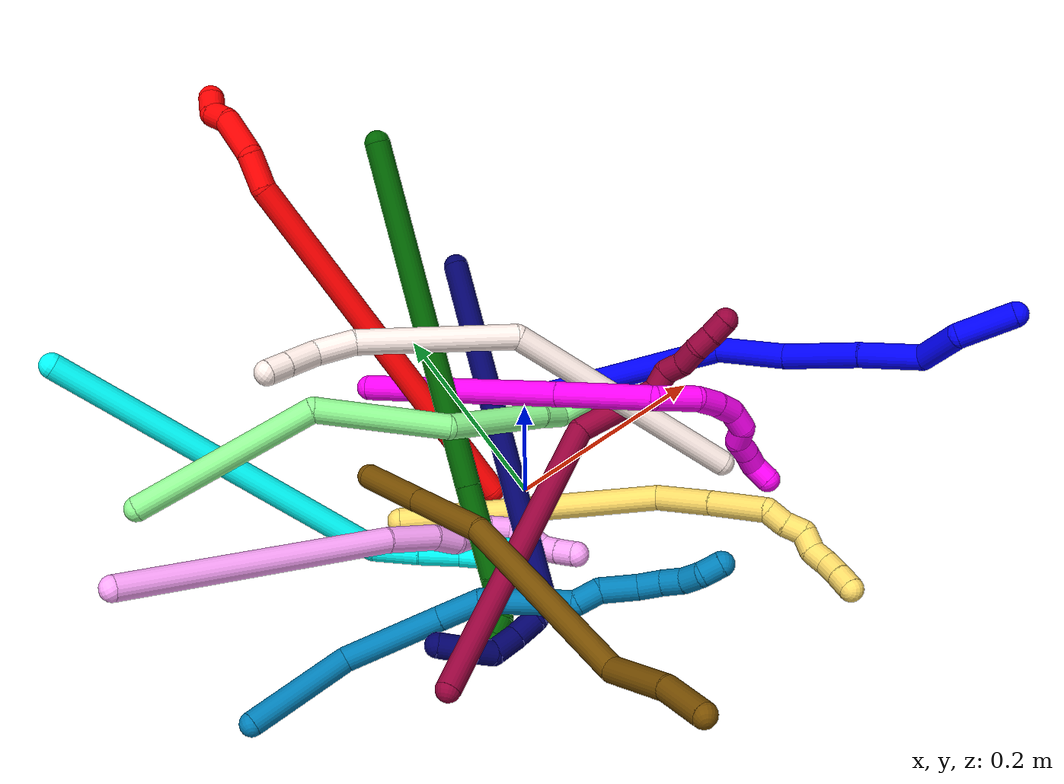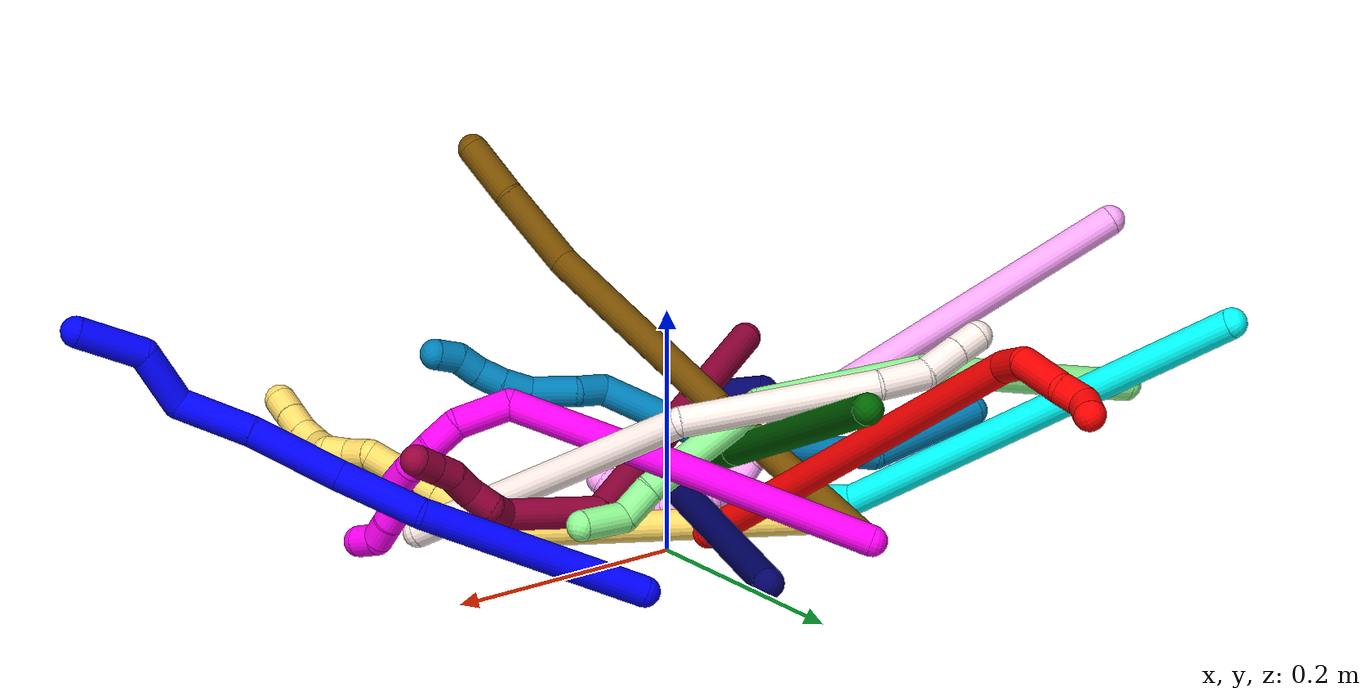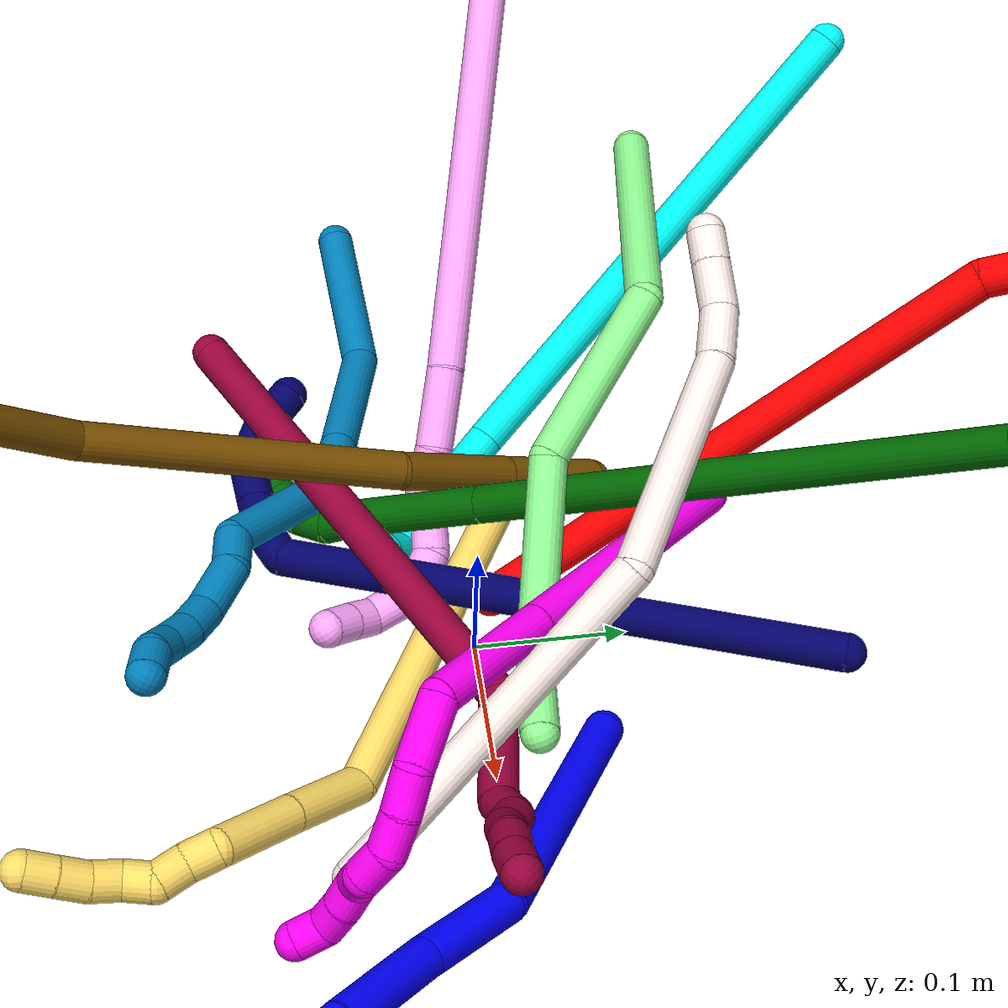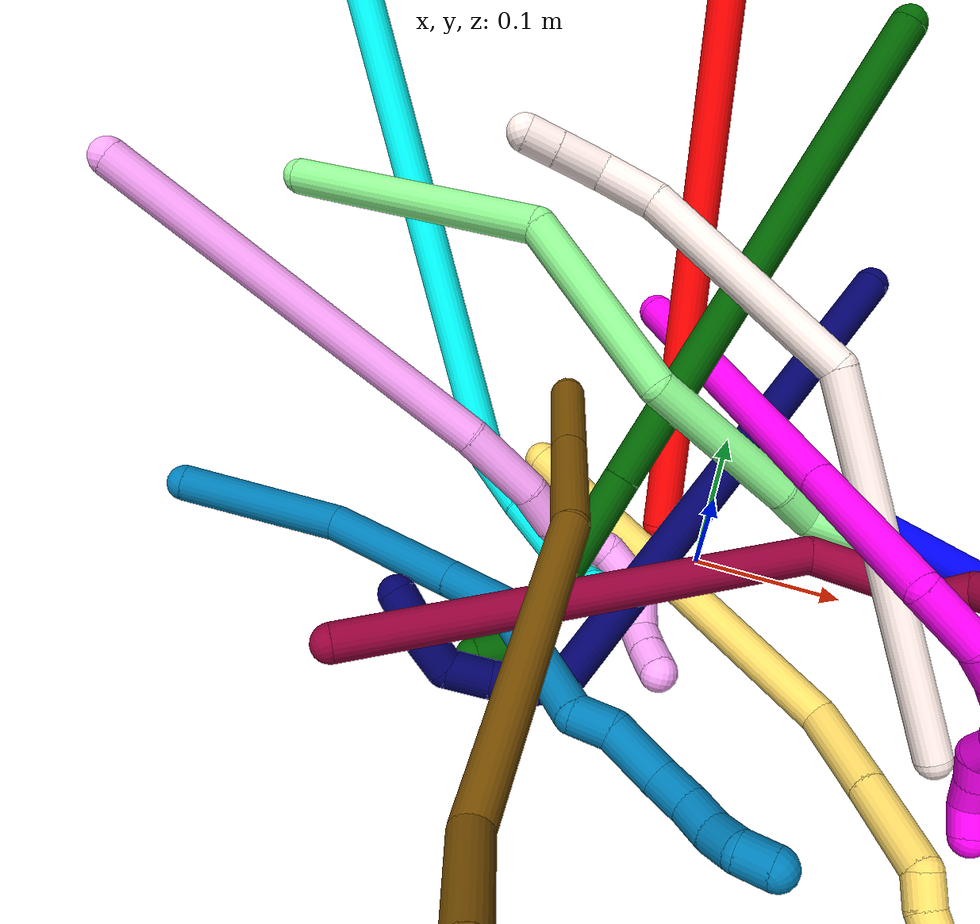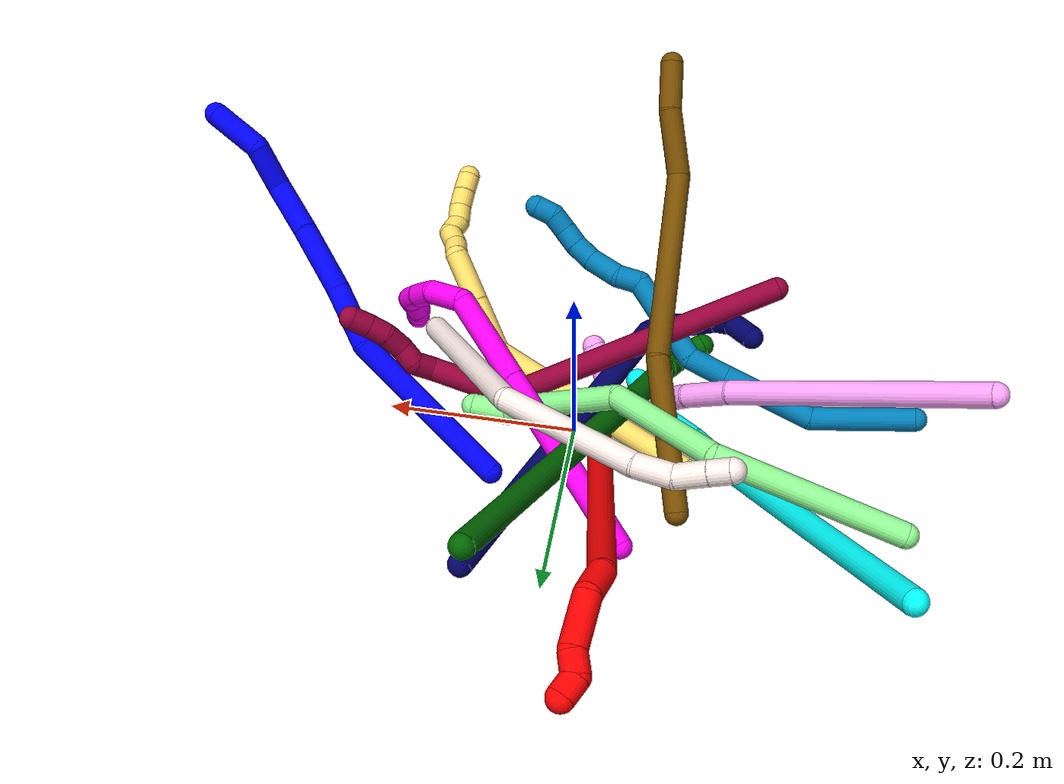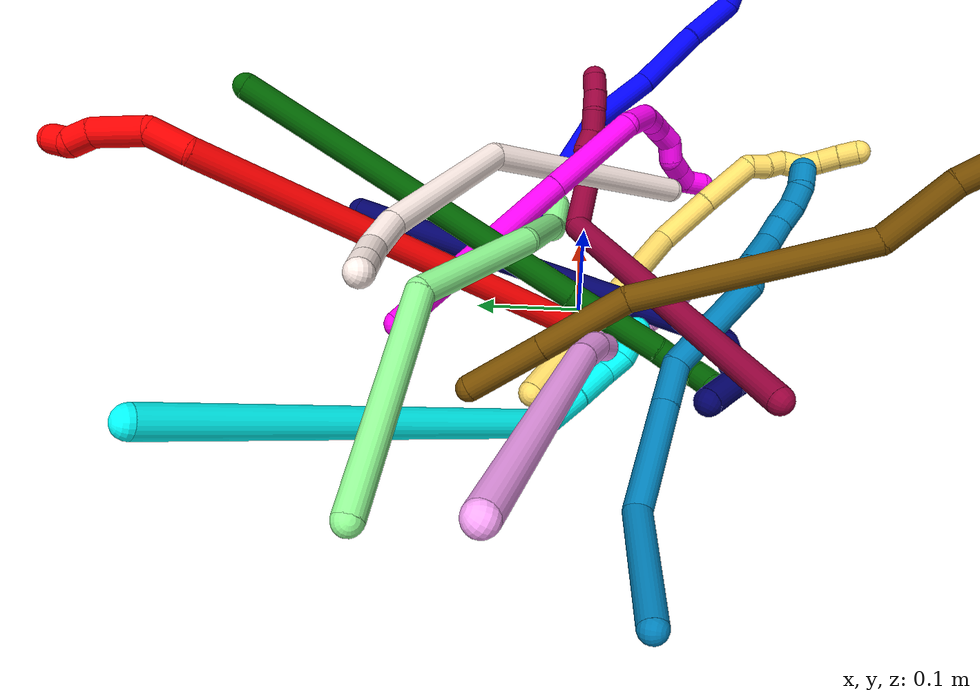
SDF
<sdf version="1.7">
 <world name="default">
  <plugin name="TubeGeneratorPlugin" filename="libtube_generator_plugin.so"/>
  <model name="photoneo_s_sensor">
   <static>1</static>
   <pose>0 0 2 1.57079 1.57079 3.14159</pose>
   <link name="link">
    <inertial><mass>0.1</mass></inertial>
    <sensor name="sensor" type="depth">
     <update_rate>30</update_rate>
     <camera>
      <horizontal_fov>1.22</horizontal_fov>
      <image><width>1920</width><height>1200</height><format>B8G8R8</format></image>
      <clip><near>0.1</near><far>4</far></clip>
      <depth_camera><output>points</output></depth_camera>
     </camera>
     <plugin name="camera_plugin" filename="libgazebo_ros_depth_camera.so">
      <baseline>0.2</baseline>
      <alwaysOn>1</alwaysOn>
      <updateRate>0.0</updateRate>
      <cameraName>camera_ir</cameraName>
      <imageTopicName>/camera/color/image_raw</imageTopicName>
      <cameraInfoTopicName>/camera/color/camera_info</cameraInfoTopicName>
      <depthImageTopicName>/camera/depth/image_raw</depthImageTopicName>
      <depthImageCameraInfoTopicName>/camera/depth/camera_info</depthImageCameraInfoTopicName>
      <pointCloudTopicName>/camera/depth/points</pointCloudTopicName>
      <frameName>fr_optical</frameName>
      <pointCloudCutoff>0.1</pointCloudCutoff>
      <pointCloudCutoffMax>2.0</pointCloudCutoffMax>
      <distortionK1>0</distortionK1>
      <distortionK2>0</distortionK2>
      <distortionK3>0</distortionK3>
      <distortionT1>0</distortionT1>
      <distortionT2>0</distortionT2>
      <CxPrime>0</CxPrime>
      <Cx>0</Cx>
      <Cy>0</Cy>
      <focalLength>0</focalLength>
      <hackBaseline>0</hackBaseline>
     </plugin>
    </sensor>
   </link>
  </model>
  <gravity>0 0 -9.8</gravity>
  <magnetic_field>6e-06 2.3e-05 -4.2e-05</magnetic_field>
  <atmosphere type="adiabatic"/>
  <physics name="default_physics" default="0" type="ode">
   <max_step_size>0.003</max_step_size>
   <real_time_factor>1</real_time_factor>
   <real_time_update_rate>1000</real_time_update_rate>
   <max_contacts>10000</max_contacts>
   <ode>
    <solver>
     <type>quick</type>
     <iters>100</iters>
     <sor>1.3</sor>
     <use_dynamic_moi_rescaling>0</use_dynamic_moi_rescaling>
    </solver>
    <constraints>
     <contact_max_correcting_vel>0</contact_max_correcting_vel>
     <contact_surface_layer>0.001</contact_surface_layer>
     <cfm>0</cfm>
     <erp>0.2</erp>
    </constraints>
   </ode>
  </physics>
  <scene><ambient>0.4 0.4 0.4 1</ambient><background>0.7 0.7 0.7 1</background><shadows>0</shadows></scene>
  <audio><device>default</device></audio>
  <spherical_coordinates>
   <surface_model>EARTH_WGS84</surface_model>
   <latitude_deg>0</latitude_deg>
   <longitude_deg>0</longitude_deg>
   <elevation>0</elevation>
   <heading_deg>0</heading_deg>
  </spherical_coordinates>
  <model name="bin">
   <static>1</static>
   <link name="bottom">
    <collision name="collision-bottom">
     <pose>0 0 -0.01 0 -0 0</pose>
     <geometry><box><size>0.8 0.6 0.02</size></box></geometry>
     <surface>
      <friction><ode><mu>100</mu><mu2>100</mu2></ode></friction>
      <contact><collide_bitmask>65535</collide_bitmask></contact>
     </surface>
    </collision>
   </link>
   <link name="west_wall">
    <collision name="collision-west_wall">
     <pose>-0.41 0 0.1 0 -0 0</pose>
     <geometry><box><size>0.02 0.6 0.2</size></box></geometry>
     <surface>
      <friction><ode><mu>100</mu><mu2>100</mu2></ode></friction>
      <contact><collide_bitmask>65535</collide_bitmask></contact>
     </surface>
    </collision>
   </link>
   <link name="east_wall">
    <collision name="collision-east_wall">
     <pose>0.41 0 0.1 0 -0 0</pose>
     <geometry><box><size>0.02 0.6 0.2</size></box></geometry>
     <surface>
      <friction><ode><mu>100</mu><mu2>100</mu2></ode></friction>
      <contact><collide_bitmask>65535</collide_bitmask></contact>
     </surface>
    </collision>
   </link>
   <link name="south_wall">
    <collision name="collision-south_wall">
     <pose>0 -0.31 0.1 0 -0 0</pose>
     <geometry><box><size>0.8 0.02 0.2</size></box></geometry>
     <surface>
      <friction><ode><mu>100</mu><mu2>100</mu2></ode></friction>
      <contact><collide_bitmask>65535</collide_bitmask></contact>
     </surface>
    </collision>
   </link>
   <link name="north_wall">
    <collision name="collision-north_wall">
     <pose>0 0.31 0.1 0 -0 0</pose>
     <geometry><box><size>0.8 0.02 0.2</size></box></geometry>
     <surface>
      <friction><ode><mu>100</mu><mu2>100</mu2></ode></friction>
      <contact><collide_bitmask>65535</collide_bitmask></contact>
     </surface>
    </collision>
   </link>
  </model>
  <model name="1">
   <static>0</static>
   <link name="1">
    <collision name="collision-cylinder-e_1_1_4">
     <pose>0.036717 -0.005946 0.086117 0.068931 0.402166 0.014056</pose>
     <geometry><cylinder><radius>0.0125</radius><length>0.187612</length></cylinder></geometry>
     <surface>
      <friction><ode><mu>1.16</mu><mu2>1.16</mu2><slip1>0</slip1><slip2>0</slip2></ode></friction>
      <contact><ode><kp>1e+06</kp><kd>1</kd><max_vel>0</max_vel><min_depth>0.001</min_depth></ode></contact>
     </surface>
    </collision>
    <visual name="visual-cylinder-e_1_1_4">
     <pose>0.036717 -0.005946 0.086117 0.068931 0.402166 0.014056</pose>
     <geometry><cylinder><radius>0.0125</radius><length>0.187612</length></cylinder></geometry>
     <material><ambient>0 0 1 1</ambient></material>
    </visual>
    <collision name="collision-cylinder-e_2_4_5">
     <pose>0.075753 -0.008967 0.207148 -0.083538 0.06611 -0.002764</pose>
     <geometry><cylinder><radius>0.0125</radius><length>0.070228</length></cylinder></geometry>
     <surface>
      <friction><ode><mu>1.16</mu><mu2>1.16</mu2><slip1>0</slip1><slip2>0</slip2></ode></friction>
      <contact><ode><kp>1e+06</kp><kd>1</kd><max_vel>0</max_vel><min_depth>0.001</min_depth></ode></contact>
     </surface>
    </collision>
    <visual name="visual-cylinder-e_2_4_5">
     <pose>0.075753 -0.008967 0.207148 -0.083538 0.06611 -0.002764</pose>
     <geometry><cylinder><radius>0.0125</radius><length>0.070228</length></cylinder></geometry>
     <material><ambient>0 0 1 1</ambient></material>
    </visual>
    <collision name="collision-cylinder-e_3_5_6">
     <pose>0.08496 -0.002168 0.279128 -0.104204 0.182741 -0.009556</pose>
     <geometry><cylinder><radius>0.0125</radius><length>0.075797</length></cylinder></geometry>
     <surface>
      <friction><ode><mu>1.16</mu><mu2>1.16</mu2><slip1>0</slip1><slip2>0</slip2></ode></friction>
      <contact><ode><kp>1e+06</kp><kd>1</kd><max_vel>0</max_vel><min_depth>0.001</min_depth></ode></contact>
     </surface>
    </collision>
    <visual name="visual-cylinder-e_3_5_6">
     <pose>0.08496 -0.002168 0.279128 -0.104204 0.182741 -0.009556</pose>
     <geometry><cylinder><radius>0.0125</radius><length>0.075797</length></cylinder></geometry>
     <material><ambient>0 0 1 1</ambient></material>
    </visual>
    <collision name="collision-cylinder-e_4_6_7">
     <pose>0.095518 0.001941 0.346478 -0.007658 0.120618 -0.000462</pose>
     <geometry><cylinder><radius>0.0125</radius><length>0.061013</length></cylinder></geometry>
     <surface>
      <friction><ode><mu>1.16</mu><mu2>1.16</mu2><slip1>0</slip1><slip2>0</slip2></ode></friction>
      <contact><ode><kp>1e+06</kp><kd>1</kd><max_vel>0</max_vel><min_depth>0.001</min_depth></ode></contact>
     </surface>
    </collision>
    <visual name="visual-cylinder-e_4_6_7">
     <pose>0.095518 0.001941 0.346478 -0.007658 0.120618 -0.000462</pose>
     <geometry><cylinder><radius>0.0125</radius><length>0.061013</length></cylinder></geometry>
     <material><ambient>0 0 1 1</ambient></material>
    </visual>
    <collision name="collision-cylinder-e_5_7_8">
     <pose>0.112862 0.013815 0.393311 -0.613069 0.594278 -0.19323</pose>
     <geometry><cylinder><radius>0.0125</radius><length>0.048843</length></cylinder></geometry>
     <surface>
      <friction><ode><mu>1.16</mu><mu2>1.16</mu2><slip1>0</slip1><slip2>0</slip2></ode></friction>
      <contact><ode><kp>1e+06</kp><kd>1</kd><max_vel>0</max_vel><min_depth>0.001</min_depth></ode></contact>
     </surface>
    </collision>
    <visual name="visual-cylinder-e_5_7_8">
     <pose>0.112862 0.013815 0.393311 -0.613069 0.594278 -0.19323</pose>
     <geometry><cylinder><radius>0.0125</radius><length>0.048843</length></cylinder></geometry>
     <material><ambient>0 0 1 1</ambient></material>
    </visual>
    <collision name="collision-cylinder-e_6_8_2">
     <pose>0.14027 0.022394 0.434361 0.124401 0.507599 0.032308</pose>
     <geometry><cylinder><radius>0.0125</radius><length>0.056508</length></cylinder></geometry>
     <surface>
      <friction><ode><mu>1.16</mu><mu2>1.16</mu2><slip1>0</slip1><slip2>0</slip2></ode></friction>
      <contact><ode><kp>1e+06</kp><kd>1</kd><max_vel>0</max_vel><min_depth>0.001</min_depth></ode></contact>
     </surface>
    </collision>
    <visual name="visual-cylinder-e_6_8_2">
     <pose>0.14027 0.022394 0.434361 0.124401 0.507599 0.032308</pose>
     <geometry><cylinder><radius>0.0125</radius><length>0.056508</length></cylinder></geometry>
     <material><ambient>0 0 1 1</ambient></material>
    </visual>
    <collision name="collision-sphere-2">
     <pose>0.154004 0.01933 0.458862 0 -0 0</pose>
     <geometry><sphere><radius>0.0125</radius></sphere></geometry>
     <surface>
      <friction><ode><mu>1.16</mu><mu2>1.16</mu2><slip1>0</slip1><slip2>0</slip2></ode></friction>
      <contact><ode><kp>1e+06</kp><kd>1</kd><max_vel>0</max_vel><min_depth>0.001</min_depth></ode></contact>
     </surface>
    </collision>
    <visual name="visual-sphere-2">
     <pose>0.154004 0.01933 0.458862 0 -0 0</pose>
     <geometry><sphere><radius>0.0125</radius></sphere></geometry>
     <material><ambient>0 0 1 1</ambient></material>
    </visual>
    <collision name="collision-sphere-4">
     <pose>0.073434 -0.011891 0.172233 0 -0 0</pose>
     <geometry><sphere><radius>0.0125</radius></sphere></geometry>
     <surface>
      <friction><ode><mu>1.16</mu><mu2>1.16</mu2><slip1>0</slip1><slip2>0</slip2></ode></friction>
      <contact><ode><kp>1e+06</kp><kd>1</kd><max_vel>0</max_vel><min_depth>0.001</min_depth></ode></contact>
     </surface>
    </collision>
    <visual name="visual-sphere-4">
     <pose>0.073434 -0.011891 0.172233 0 -0 0</pose>
     <geometry><sphere><radius>0.0125</radius></sphere></geometry>
     <material><ambient>0 0 1 1</ambient></material>
    </visual>
    <collision name="collision-sphere-1">
     <geometry><sphere><radius>0.0125</radius></sphere></geometry>
     <surface>
      <friction><ode><mu>1.16</mu><mu2>1.16</mu2><slip1>0</slip1><slip2>0</slip2></ode></friction>
      <contact><ode><kp>1e+06</kp><kd>1</kd><max_vel>0</max_vel><min_depth>0.001</min_depth></ode></contact>
     </surface>
    </collision>
    <visual name="visual-sphere-1">
     <geometry><sphere><radius>0.0125</radius></sphere></geometry>
     <material><ambient>0 0 1 1</ambient></material>
    </visual>
    <collision name="collision-sphere-8">
     <pose>0.126536 0.025458 0.409861 0 -0 0</pose>
     <geometry><sphere><radius>0.0125</radius></sphere></geometry>
     <surface>
      <friction><ode><mu>1.16</mu><mu2>1.16</mu2><slip1>0</slip1><slip2>0</slip2></ode></friction>
      <contact><ode><kp>1e+06</kp><kd>1</kd><max_vel>0</max_vel><min_depth>0.001</min_depth></ode></contact>
     </surface>
    </collision>
    <visual name="visual-sphere-8">
     <pose>0.126536 0.025458 0.409861 0 -0 0</pose>
     <geometry><sphere><radius>0.0125</radius></sphere></geometry>
     <material><ambient>0 0 1 1</ambient></material>
    </visual>
    <collision name="collision-sphere-5">
     <pose>0.078073 -0.006044 0.242063 0 -0 0</pose>
     <geometry><sphere><radius>0.0125</radius></sphere></geometry>
     <surface>
      <friction><ode><mu>1.16</mu><mu2>1.16</mu2><slip1>0</slip1><slip2>0</slip2></ode></friction>
      <contact><ode><kp>1e+06</kp><kd>1</kd><max_vel>0</max_vel><min_depth>0.001</min_depth></ode></contact>
     </surface>
    </collision>
    <visual name="visual-sphere-5">
     <pose>0.078073 -0.006044 0.242063 0 -0 0</pose>
     <geometry><sphere><radius>0.0125</radius></sphere></geometry>
     <material><ambient>0 0 1 1</ambient></material>
    </visual>
    <collision name="collision-sphere-6">
     <pose>0.091847 0.001709 0.316194 0 -0 0</pose>
     <geometry><sphere><radius>0.0125</radius></sphere></geometry>
     <surface>
      <friction><ode><mu>1.16</mu><mu2>1.16</mu2><slip1>0</slip1><slip2>0</slip2></ode></friction>
      <contact><ode><kp>1e+06</kp><kd>1</kd><max_vel>0</max_vel><min_depth>0.001</min_depth></ode></contact>
     </surface>
    </collision>
    <visual name="visual-sphere-6">
     <pose>0.091847 0.001709 0.316194 0 -0 0</pose>
     <geometry><sphere><radius>0.0125</radius></sphere></geometry>
     <material><ambient>0 0 1 1</ambient></material>
    </visual>
    <collision name="collision-sphere-7">
     <pose>0.099189 0.002173 0.376762 0 -0 0</pose>
     <geometry><sphere><radius>0.0125</radius></sphere></geometry>
     <surface>
      <friction><ode><mu>1.16</mu><mu2>1.16</mu2><slip1>0</slip1><slip2>0</slip2></ode></friction>
      <contact><ode><kp>1e+06</kp><kd>1</kd><max_vel>0</max_vel><min_depth>0.001</min_depth></ode></contact>
     </surface>
    </collision>
    <visual name="visual-sphere-7">
     <pose>0.099189 0.002173 0.376762 0 -0 0</pose>
     <geometry><sphere><radius>0.0125</radius></sphere></geometry>
     <material><ambient>0 0 1 1</ambient></material>
    </visual>
    <inertial>
     <pose>0.07583 0.000298 0.233512 0 -0 0</pose>
     <mass>0.5</mass>
     <inertia>
      <ixx>0.000646</ixx>
      <ixy>0</ixy>
      <ixz>0</ixz>
      <iyy>0.000682</iyy>
      <iyz>0</iyz>
      <izz>-0.000184</izz>
     </inertia>
    </inertial>
   </link>
   <pose>0.075754 0.072178 0.00497 1.27505 -0.570965 0.80849</pose>
  </model>
  <model name="2">
   <static>0</static>
   <link name="2">
    <collision name="collision-cylinder-e_1_1_4">
     <pose>0.016043 0.044769 0.181571 -0.241745 0.085577 -0.010401</pose>
     <geometry><cylinder><radius>0.0125</radius><length>0.375391</length></cylinder></geometry>
     <surface>
      <friction><ode><mu>1.16</mu><mu2>1.16</mu2><slip1>0</slip1><slip2>0</slip2></ode></friction>
      <contact><ode><kp>1e+06</kp><kd>1</kd><max_vel>0</max_vel><min_depth>0.001</min_depth></ode></contact>
     </surface>
    </collision>
    <visual name="visual-cylinder-e_1_1_4">
     <pose>0.016043 0.044769 0.181571 -0.241745 0.085577 -0.010401</pose>
     <geometry><cylinder><radius>0.0125</radius><length>0.375391</length></cylinder></geometry>
     <material><ambient>1 0 0 1</ambient></material>
    </visual>
    <collision name="collision-cylinder-e_2_4_5">
     <pose>0.028187 0.097234 0.378322 -0.469151 -0.225185 0.054029</pose>
     <geometry><cylinder><radius>0.0125</radius><length>0.03492</length></cylinder></geometry>
     <surface>
      <friction><ode><mu>1.16</mu><mu2>1.16</mu2><slip1>0</slip1><slip2>0</slip2></ode></friction>
      <contact><ode><kp>1e+06</kp><kd>1</kd><max_vel>0</max_vel><min_depth>0.001</min_depth></ode></contact>
     </surface>
    </collision>
    <visual name="visual-cylinder-e_2_4_5">
     <pose>0.028187 0.097234 0.378322 -0.469151 -0.225185 0.054029</pose>
     <geometry><cylinder><radius>0.0125</radius><length>0.03492</length></cylinder></geometry>
     <material><ambient>1 0 0 1</ambient></material>
    </visual>
    <collision name="collision-cylinder-e_3_5_6">
     <pose>0.009051 0.107892 0.412308 -0.156276 -0.674955 0.054936</pose>
     <geometry><cylinder><radius>0.0125</radius><length>0.04877</length></cylinder></geometry>
     <surface>
      <friction><ode><mu>1.16</mu><mu2>1.16</mu2><slip1>0</slip1><slip2>0</slip2></ode></friction>
      <contact><ode><kp>1e+06</kp><kd>1</kd><max_vel>0</max_vel><min_depth>0.001</min_depth></ode></contact>
     </surface>
    </collision>
    <visual name="visual-cylinder-e_3_5_6">
     <pose>0.009051 0.107892 0.412308 -0.156276 -0.674955 0.054936</pose>
     <geometry><cylinder><radius>0.0125</radius><length>0.04877</length></cylinder></geometry>
     <material><ambient>1 0 0 1</ambient></material>
    </visual>
    <collision name="collision-cylinder-e_4_6_7">
     <pose>-0.012422 0.107713 0.438738 0.390958 -0.647507 -0.132692</pose>
     <geometry><cylinder><radius>0.0125</radius><length>0.020674</length></cylinder></geometry>
     <surface>
      <friction><ode><mu>1.16</mu><mu2>1.16</mu2><slip1>0</slip1><slip2>0</slip2></ode></friction>
      <contact><ode><kp>1e+06</kp><kd>1</kd><max_vel>0</max_vel><min_depth>0.001</min_depth></ode></contact>
     </surface>
    </collision>
    <visual name="visual-cylinder-e_4_6_7">
     <pose>-0.012422 0.107713 0.438738 0.390958 -0.647507 -0.132692</pose>
     <geometry><cylinder><radius>0.0125</radius><length>0.020674</length></cylinder></geometry>
     <material><ambient>1 0 0 1</ambient></material>
    </visual>
    <collision name="collision-cylinder-e_5_7_2">
     <pose>-0.026008 0.10878 0.451902 -0.649466 -0.812792 0.287755</pose>
     <geometry><cylinder><radius>0.0125</radius><length>0.020244</length></cylinder></geometry>
     <surface>
      <friction><ode><mu>1.16</mu><mu2>1.16</mu2><slip1>0</slip1><slip2>0</slip2></ode></friction>
      <contact><ode><kp>1e+06</kp><kd>1</kd><max_vel>0</max_vel><min_depth>0.001</min_depth></ode></contact>
     </surface>
    </collision>
    <visual name="visual-cylinder-e_5_7_2">
     <pose>-0.026008 0.10878 0.451902 -0.649466 -0.812792 0.287755</pose>
     <geometry><cylinder><radius>0.0125</radius><length>0.020244</length></cylinder></geometry>
     <material><ambient>1 0 0 1</ambient></material>
    </visual>
    <collision name="collision-sphere-2">
     <pose>-0.033359 0.112988 0.457444 0 -0 0</pose>
     <geometry><sphere><radius>0.0125</radius></sphere></geometry>
     <surface>
      <friction><ode><mu>1.16</mu><mu2>1.16</mu2><slip1>0</slip1><slip2>0</slip2></ode></friction>
      <contact><ode><kp>1e+06</kp><kd>1</kd><max_vel>0</max_vel><min_depth>0.001</min_depth></ode></contact>
     </surface>
    </collision>
    <visual name="visual-sphere-2">
     <pose>-0.033359 0.112988 0.457444 0 -0 0</pose>
     <geometry><sphere><radius>0.0125</radius></sphere></geometry>
     <material><ambient>1 0 0 1</ambient></material>
    </visual>
    <collision name="collision-sphere-7">
     <pose>-0.018657 0.104571 0.44636 0 -0 0</pose>
     <geometry><sphere><radius>0.0125</radius></sphere></geometry>
     <surface>
      <friction><ode><mu>1.16</mu><mu2>1.16</mu2><slip1>0</slip1><slip2>0</slip2></ode></friction>
      <contact><ode><kp>1e+06</kp><kd>1</kd><max_vel>0</max_vel><min_depth>0.001</min_depth></ode></contact>
     </surface>
    </collision>
    <visual name="visual-sphere-7">
     <pose>-0.018657 0.104571 0.44636 0 -0 0</pose>
     <geometry><sphere><radius>0.0125</radius></sphere></geometry>
     <material><ambient>1 0 0 1</ambient></material>
    </visual>
    <collision name="collision-sphere-6">
     <pose>-0.006187 0.110855 0.431115 0 -0 0</pose>
     <geometry><sphere><radius>0.0125</radius></sphere></geometry>
     <surface>
      <friction><ode><mu>1.16</mu><mu2>1.16</mu2><slip1>0</slip1><slip2>0</slip2></ode></friction>
      <contact><ode><kp>1e+06</kp><kd>1</kd><max_vel>0</max_vel><min_depth>0.001</min_depth></ode></contact>
     </surface>
    </collision>
    <visual name="visual-sphere-6">
     <pose>-0.006187 0.110855 0.431115 0 -0 0</pose>
     <geometry><sphere><radius>0.0125</radius></sphere></geometry>
     <material><ambient>1 0 0 1</ambient></material>
    </visual>
    <collision name="collision-sphere-5">
     <pose>0.024288 0.104929 0.393502 0 -0 0</pose>
     <geometry><sphere><radius>0.0125</radius></sphere></geometry>
     <surface>
      <friction><ode><mu>1.16</mu><mu2>1.16</mu2><slip1>0</slip1><slip2>0</slip2></ode></friction>
      <contact><ode><kp>1e+06</kp><kd>1</kd><max_vel>0</max_vel><min_depth>0.001</min_depth></ode></contact>
     </surface>
    </collision>
    <visual name="visual-sphere-5">
     <pose>0.024288 0.104929 0.393502 0 -0 0</pose>
     <geometry><sphere><radius>0.0125</radius></sphere></geometry>
     <material><ambient>1 0 0 1</ambient></material>
    </visual>
    <collision name="collision-sphere-1">
     <geometry><sphere><radius>0.0125</radius></sphere></geometry>
     <surface>
      <friction><ode><mu>1.16</mu><mu2>1.16</mu2><slip1>0</slip1><slip2>0</slip2></ode></friction>
      <contact><ode><kp>1e+06</kp><kd>1</kd><max_vel>0</max_vel><min_depth>0.001</min_depth></ode></contact>
     </surface>
    </collision>
    <visual name="visual-sphere-1">
     <geometry><sphere><radius>0.0125</radius></sphere></geometry>
     <material><ambient>1 0 0 1</ambient></material>
    </visual>
    <collision name="collision-sphere-4">
     <pose>0.032085 0.089539 0.363141 0 -0 0</pose>
     <geometry><sphere><radius>0.0125</radius></sphere></geometry>
     <surface>
      <friction><ode><mu>1.16</mu><mu2>1.16</mu2><slip1>0</slip1><slip2>0</slip2></ode></friction>
      <contact><ode><kp>1e+06</kp><kd>1</kd><max_vel>0</max_vel><min_depth>0.001</min_depth></ode></contact>
     </surface>
    </collision>
    <visual name="visual-sphere-4">
     <pose>0.032085 0.089539 0.363141 0 -0 0</pose>
     <geometry><sphere><radius>0.0125</radius></sphere></geometry>
     <material><ambient>1 0 0 1</ambient></material>
    </visual>
    <inertial>
     <pose>0.013329 0.059785 0.239397 0 -0 0</pose>
     <mass>0.5</mass>
     <inertia>
      <ixx>0.004375</ixx>
      <ixy>0</ixy>
      <ixz>0</ixz>
      <iyy>0.004278</iyy>
      <iyz>0</iyz>
      <izz>-0.001391</izz>
     </inertia>
    </inertial>
   </link>
   <pose>-0.029844 0.014866 0.012471 0.843992 -0.907898 -2.17444</pose>
  </model>
  <model name="3">
   <static>0</static>
   <link name="3">
    <collision name="collision-cylinder-e_1_1_4">
     <pose>-0.002557 0.009115 -0.179802 -3.09094 -0.014202 0.546627</pose>
     <geometry><cylinder><radius>0.0125</radius><length>0.360103</length></cylinder></geometry>
     <surface>
      <friction><ode><mu>1.16</mu><mu2>1.16</mu2><slip1>0</slip1><slip2>0</slip2></ode></friction>
      <contact><ode><kp>1e+06</kp><kd>1</kd><max_vel>0</max_vel><min_depth>0.001</min_depth></ode></contact>
     </surface>
    </collision>
    <visual name="visual-cylinder-e_1_1_4">
     <pose>-0.002557 0.009115 -0.179802 -3.09094 -0.014202 0.546627</pose>
     <geometry><cylinder><radius>0.0125</radius><length>0.360103</length></cylinder></geometry>
     <material><ambient>0.003922 1 0.996078 1</ambient></material>
    </visual>
    <collision name="collision-cylinder-e_2_4_5">
     <pose>0.003543 0.010637 -0.378494 2.75937 0.402071 1.62271</pose>
     <geometry><cylinder><radius>0.0125</radius><length>0.044245</length></cylinder></geometry>
     <surface>
      <friction><ode><mu>1.16</mu><mu2>1.16</mu2><slip1>0</slip1><slip2>0</slip2></ode></friction>
      <contact><ode><kp>1e+06</kp><kd>1</kd><max_vel>0</max_vel><min_depth>0.001</min_depth></ode></contact>
     </surface>
    </collision>
    <visual name="visual-cylinder-e_2_4_5">
     <pose>0.003543 0.010637 -0.378494 2.75937 0.402071 1.62271</pose>
     <geometry><cylinder><radius>0.0125</radius><length>0.044245</length></cylinder></geometry>
     <material><ambient>0.003922 1 0.996078 1</ambient></material>
    </visual>
    <collision name="collision-cylinder-e_3_5_6">
     <pose>0.021004 -0.002177 -0.414797 2.85032 0.450987 2.00382</pose>
     <geometry><cylinder><radius>0.0125</radius><length>0.040399</length></cylinder></geometry>
     <surface>
      <friction><ode><mu>1.16</mu><mu2>1.16</mu2><slip1>0</slip1><slip2>0</slip2></ode></friction>
      <contact><ode><kp>1e+06</kp><kd>1</kd><max_vel>0</max_vel><min_depth>0.001</min_depth></ode></contact>
     </surface>
    </collision>
    <visual name="visual-cylinder-e_3_5_6">
     <pose>0.021004 -0.002177 -0.414797 2.85032 0.450987 2.00382</pose>
     <geometry><cylinder><radius>0.0125</radius><length>0.040399</length></cylinder></geometry>
     <material><ambient>0.003922 1 0.996078 1</ambient></material>
    </visual>
    <collision name="collision-cylinder-e_4_6_7">
     <pose>0.03496 -0.01293 -0.443409 2.68275 0.391181 1.40711</pose>
     <geometry><cylinder><radius>0.0125</radius><length>0.02702</length></cylinder></geometry>
     <surface>
      <friction><ode><mu>1.16</mu><mu2>1.16</mu2><slip1>0</slip1><slip2>0</slip2></ode></friction>
      <contact><ode><kp>1e+06</kp><kd>1</kd><max_vel>0</max_vel><min_depth>0.001</min_depth></ode></contact>
     </surface>
    </collision>
    <visual name="visual-cylinder-e_4_6_7">
     <pose>0.03496 -0.01293 -0.443409 2.68275 0.391181 1.40711</pose>
     <geometry><cylinder><radius>0.0125</radius><length>0.02702</length></cylinder></geometry>
     <material><ambient>0.003922 1 0.996078 1</ambient></material>
    </visual>
    <collision name="collision-cylinder-e_5_7_2">
     <pose>0.046785 -0.030478 -0.457822 1.83226 0.492462 0.632852</pose>
     <geometry><cylinder><radius>0.0125</radius><length>0.028233</length></cylinder></geometry>
     <surface>
      <friction><ode><mu>1.16</mu><mu2>1.16</mu2><slip1>0</slip1><slip2>0</slip2></ode></friction>
      <contact><ode><kp>1e+06</kp><kd>1</kd><max_vel>0</max_vel><min_depth>0.001</min_depth></ode></contact>
     </surface>
    </collision>
    <visual name="visual-cylinder-e_5_7_2">
     <pose>0.046785 -0.030478 -0.457822 1.83226 0.492462 0.632852</pose>
     <geometry><cylinder><radius>0.0125</radius><length>0.028233</length></cylinder></geometry>
     <material><ambient>0.003922 1 0.996078 1</ambient></material>
    </visual>
    <collision name="collision-sphere-2">
     <pose>0.053459 -0.042494 -0.461038 0 -0 0</pose>
     <geometry><sphere><radius>0.0125</radius></sphere></geometry>
     <surface>
      <friction><ode><mu>1.16</mu><mu2>1.16</mu2><slip1>0</slip1><slip2>0</slip2></ode></friction>
      <contact><ode><kp>1e+06</kp><kd>1</kd><max_vel>0</max_vel><min_depth>0.001</min_depth></ode></contact>
     </surface>
    </collision>
    <visual name="visual-sphere-2">
     <pose>0.053459 -0.042494 -0.461038 0 -0 0</pose>
     <geometry><sphere><radius>0.0125</radius></sphere></geometry>
     <material><ambient>0.003922 1 0.996078 1</ambient></material>
    </visual>
    <collision name="collision-sphere-7">
     <pose>0.040111 -0.018462 -0.454607 0 -0 0</pose>
     <geometry><sphere><radius>0.0125</radius></sphere></geometry>
     <surface>
      <friction><ode><mu>1.16</mu><mu2>1.16</mu2><slip1>0</slip1><slip2>0</slip2></ode></friction>
      <contact><ode><kp>1e+06</kp><kd>1</kd><max_vel>0</max_vel><min_depth>0.001</min_depth></ode></contact>
     </surface>
    </collision>
    <visual name="visual-sphere-7">
     <pose>0.040111 -0.018462 -0.454607 0 -0 0</pose>
     <geometry><sphere><radius>0.0125</radius></sphere></geometry>
     <material><ambient>0.003922 1 0.996078 1</ambient></material>
    </visual>
    <collision name="collision-sphere-6">
     <pose>0.029808 -0.007398 -0.432211 0 -0 0</pose>
     <geometry><sphere><radius>0.0125</radius></sphere></geometry>
     <surface>
      <friction><ode><mu>1.16</mu><mu2>1.16</mu2><slip1>0</slip1><slip2>0</slip2></ode></friction>
      <contact><ode><kp>1e+06</kp><kd>1</kd><max_vel>0</max_vel><min_depth>0.001</min_depth></ode></contact>
     </surface>
    </collision>
    <visual name="visual-sphere-6">
     <pose>0.029808 -0.007398 -0.432211 0 -0 0</pose>
     <geometry><sphere><radius>0.0125</radius></sphere></geometry>
     <material><ambient>0.003922 1 0.996078 1</ambient></material>
    </visual>
    <collision name="collision-sphere-5">
     <pose>0.0122 0.003043 -0.397383 0 -0 0</pose>
     <geometry><sphere><radius>0.0125</radius></sphere></geometry>
     <surface>
      <friction><ode><mu>1.16</mu><mu2>1.16</mu2><slip1>0</slip1><slip2>0</slip2></ode></friction>
      <contact><ode><kp>1e+06</kp><kd>1</kd><max_vel>0</max_vel><min_depth>0.001</min_depth></ode></contact>
     </surface>
    </collision>
    <visual name="visual-sphere-5">
     <pose>0.0122 0.003043 -0.397383 0 -0 0</pose>
     <geometry><sphere><radius>0.0125</radius></sphere></geometry>
     <material><ambient>0.003922 1 0.996078 1</ambient></material>
    </visual>
    <collision name="collision-sphere-1">
     <geometry><sphere><radius>0.0125</radius></sphere></geometry>
     <surface>
      <friction><ode><mu>1.16</mu><mu2>1.16</mu2><slip1>0</slip1><slip2>0</slip2></ode></friction>
      <contact><ode><kp>1e+06</kp><kd>1</kd><max_vel>0</max_vel><min_depth>0.001</min_depth></ode></contact>
     </surface>
    </collision>
    <visual name="visual-sphere-1">
     <geometry><sphere><radius>0.0125</radius></sphere></geometry>
     <material><ambient>0.003922 1 0.996078 1</ambient></material>
    </visual>
    <collision name="collision-sphere-4">
     <pose>-0.005114 0.01823 -0.359605 0 -0 0</pose>
     <geometry><sphere><radius>0.0125</radius></sphere></geometry>
     <surface>
      <friction><ode><mu>1.16</mu><mu2>1.16</mu2><slip1>0</slip1><slip2>0</slip2></ode></friction>
      <contact><ode><kp>1e+06</kp><kd>1</kd><max_vel>0</max_vel><min_depth>0.001</min_depth></ode></contact>
     </surface>
    </collision>
    <visual name="visual-sphere-4">
     <pose>-0.005114 0.01823 -0.359605 0 -0 0</pose>
     <geometry><sphere><radius>0.0125</radius></sphere></geometry>
     <material><ambient>0.003922 1 0.996078 1</ambient></material>
    </visual>
    <inertial>
     <pose>0.0047 0.00491 -0.246316 0 -0 0</pose>
     <mass>0.5</mass>
     <inertia>
      <ixx>0.005387</ixx>
      <ixy>0</ixy>
      <ixz>0</ixz>
      <iyy>-0.00128</iyy>
      <iyz>0</iyz>
      <izz>-0.000179</izz>
     </inertia>
    </inertial>
   </link>
   <pose>-0.332529 0.287146 0.200442 -1.06488 -0.254092 0.447919</pose>
  </model>
  <model name="4">
   <static>0</static>
   <link name="4">
    <collision name="collision-cylinder-e_1_1_4">
     <pose>0.117311 -0.040926 -0.056853 2.51767 1.03248 2.10819</pose>
     <geometry><cylinder><radius>0.0125</radius><length>0.273269</length></cylinder></geometry>
     <surface>
      <friction><ode><mu>1.16</mu><mu2>1.16</mu2><slip1>0</slip1><slip2>0</slip2></ode></friction>
      <contact><ode><kp>1e+06</kp><kd>1</kd><max_vel>0</max_vel><min_depth>0.001</min_depth></ode></contact>
     </surface>
    </collision>
    <visual name="visual-cylinder-e_1_1_4">
     <pose>0.117311 -0.040926 -0.056853 2.51767 1.03248 2.10819</pose>
     <geometry><cylinder><radius>0.0125</radius><length>0.273269</length></cylinder></geometry>
     <material><ambient>1 0.65098 0.996078 1</ambient></material>
    </visual>
    <collision name="collision-cylinder-e_2_4_5">
     <pose>0.257011 -0.086793 -0.127169 2.78976 1.00113 2.51324</pose>
     <geometry><cylinder><radius>0.0125</radius><length>0.053176</length></cylinder></geometry>
     <surface>
      <friction><ode><mu>1.16</mu><mu2>1.16</mu2><slip1>0</slip1><slip2>0</slip2></ode></friction>
      <contact><ode><kp>1e+06</kp><kd>1</kd><max_vel>0</max_vel><min_depth>0.001</min_depth></ode></contact>
     </surface>
    </collision>
    <visual name="visual-cylinder-e_2_4_5">
     <pose>0.257011 -0.086793 -0.127169 2.78976 1.00113 2.51324</pose>
     <geometry><cylinder><radius>0.0125</radius><length>0.053176</length></cylinder></geometry>
     <material><ambient>1 0.65098 0.996078 1</ambient></material>
    </visual>
    <collision name="collision-cylinder-e_3_5_6">
     <pose>0.290096 -0.092368 -0.149926 3.07364 0.854216 2.99252</pose>
     <geometry><cylinder><radius>0.0125</radius><length>0.028369</length></cylinder></geometry>
     <surface>
      <friction><ode><mu>1.16</mu><mu2>1.16</mu2><slip1>0</slip1><slip2>0</slip2></ode></friction>
      <contact><ode><kp>1e+06</kp><kd>1</kd><max_vel>0</max_vel><min_depth>0.001</min_depth></ode></contact>
     </surface>
    </collision>
    <visual name="visual-cylinder-e_3_5_6">
     <pose>0.290096 -0.092368 -0.149926 3.07364 0.854216 2.99252</pose>
     <geometry><cylinder><radius>0.0125</radius><length>0.028369</length></cylinder></geometry>
     <material><ambient>1 0.65098 0.996078 1</ambient></material>
    </visual>
    <collision name="collision-cylinder-e_4_6_7">
     <pose>0.310275 -0.091978 -0.162432 -2.83344 1.22935 -2.70846</pose>
     <geometry><cylinder><radius>0.0125</radius><length>0.020127</length></cylinder></geometry>
     <surface>
      <friction><ode><mu>1.16</mu><mu2>1.16</mu2><slip1>0</slip1><slip2>0</slip2></ode></friction>
      <contact><ode><kp>1e+06</kp><kd>1</kd><max_vel>0</max_vel><min_depth>0.001</min_depth></ode></contact>
     </surface>
    </collision>
    <visual name="visual-cylinder-e_4_6_7">
     <pose>0.310275 -0.091978 -0.162432 -2.83344 1.22935 -2.70846</pose>
     <geometry><cylinder><radius>0.0125</radius><length>0.020127</length></cylinder></geometry>
     <material><ambient>1 0.65098 0.996078 1</ambient></material>
    </visual>
    <collision name="collision-cylinder-e_5_7_8">
     <pose>0.330973 -0.095346 -0.168135 2.08717 1.14789 1.67547</pose>
     <geometry><cylinder><radius>0.0125</radius><length>0.024599</length></cylinder></geometry>
     <surface>
      <friction><ode><mu>1.16</mu><mu2>1.16</mu2><slip1>0</slip1><slip2>0</slip2></ode></friction>
      <contact><ode><kp>1e+06</kp><kd>1</kd><max_vel>0</max_vel><min_depth>0.001</min_depth></ode></contact>
     </surface>
    </collision>
    <visual name="visual-cylinder-e_5_7_8">
     <pose>0.330973 -0.095346 -0.168135 2.08717 1.14789 1.67547</pose>
     <geometry><cylinder><radius>0.0125</radius><length>0.024599</length></cylinder></geometry>
     <material><ambient>1 0.65098 0.996078 1</ambient></material>
    </visual>
    <collision name="collision-cylinder-e_6_8_9">
     <pose>0.348949 -0.104103 -0.176618 2.51172 0.739265 1.74328</pose>
     <geometry><cylinder><radius>0.0125</radius><length>0.020065</length></cylinder></geometry>
     <surface>
      <friction><ode><mu>1.16</mu><mu2>1.16</mu2><slip1>0</slip1><slip2>0</slip2></ode></friction>
      <contact><ode><kp>1e+06</kp><kd>1</kd><max_vel>0</max_vel><min_depth>0.001</min_depth></ode></contact>
     </surface>
    </collision>
    <visual name="visual-cylinder-e_6_8_9">
     <pose>0.348949 -0.104103 -0.176618 2.51172 0.739265 1.74328</pose>
     <geometry><cylinder><radius>0.0125</radius><length>0.020065</length></cylinder></geometry>
     <material><ambient>1 0.65098 0.996078 1</ambient></material>
    </visual>
    <collision name="collision-cylinder-e_7_9_10">
     <pose>0.359219 -0.11493 -0.189415 2.38219 0.358061 0.851487</pose>
     <geometry><cylinder><radius>0.0125</radius><length>0.020039</length></cylinder></geometry>
     <surface>
      <friction><ode><mu>1.16</mu><mu2>1.16</mu2><slip1>0</slip1><slip2>0</slip2></ode></friction>
      <contact><ode><kp>1e+06</kp><kd>1</kd><max_vel>0</max_vel><min_depth>0.001</min_depth></ode></contact>
     </surface>
    </collision>
    <visual name="visual-cylinder-e_7_9_10">
     <pose>0.359219 -0.11493 -0.189415 2.38219 0.358061 0.851487</pose>
     <geometry><cylinder><radius>0.0125</radius><length>0.020039</length></cylinder></geometry>
     <material><ambient>1 0.65098 0.996078 1</ambient></material>
    </visual>
    <collision name="collision-cylinder-e_8_10_11">
     <pose>0.363648 -0.125676 -0.205388 2.70432 0.090397 0.401643</pose>
     <geometry><cylinder><radius>0.0125</radius><length>0.020321</length></cylinder></geometry>
     <surface>
      <friction><ode><mu>1.16</mu><mu2>1.16</mu2><slip1>0</slip1><slip2>0</slip2></ode></friction>
      <contact><ode><kp>1e+06</kp><kd>1</kd><max_vel>0</max_vel><min_depth>0.001</min_depth></ode></contact>
     </surface>
    </collision>
    <visual name="visual-cylinder-e_8_10_11">
     <pose>0.363648 -0.125676 -0.205388 2.70432 0.090397 0.401643</pose>
     <geometry><cylinder><radius>0.0125</radius><length>0.020321</length></cylinder></geometry>
     <material><ambient>1 0.65098 0.996078 1</ambient></material>
    </visual>
    <collision name="collision-cylinder-e_9_11_12">
     <pose>0.363839 -0.13926 -0.218172 1.94177 -0.072615 -0.106108</pose>
     <geometry><cylinder><radius>0.0125</radius><length>0.020009</length></cylinder></geometry>
     <surface>
      <friction><ode><mu>1.16</mu><mu2>1.16</mu2><slip1>0</slip1><slip2>0</slip2></ode></friction>
      <contact><ode><kp>1e+06</kp><kd>1</kd><max_vel>0</max_vel><min_depth>0.001</min_depth></ode></contact>
     </surface>
    </collision>
    <visual name="visual-cylinder-e_9_11_12">
     <pose>0.363839 -0.13926 -0.218172 1.94177 -0.072615 -0.106108</pose>
     <geometry><cylinder><radius>0.0125</radius><length>0.020009</length></cylinder></geometry>
     <material><ambient>1 0.65098 0.996078 1</ambient></material>
    </visual>
    <collision name="collision-cylinder-e_10_12_2">
     <pose>0.36283 -0.158023 -0.225047 1.90231 -0.028355 -0.039745</pose>
     <geometry><cylinder><radius>0.0125</radius><length>0.020026</length></cylinder></geometry>
     <surface>
      <friction><ode><mu>1.16</mu><mu2>1.16</mu2><slip1>0</slip1><slip2>0</slip2></ode></friction>
      <contact><ode><kp>1e+06</kp><kd>1</kd><max_vel>0</max_vel><min_depth>0.001</min_depth></ode></contact>
     </surface>
    </collision>
    <visual name="visual-cylinder-e_10_12_2">
     <pose>0.36283 -0.158023 -0.225047 1.90231 -0.028355 -0.039745</pose>
     <geometry><cylinder><radius>0.0125</radius><length>0.020026</length></cylinder></geometry>
     <material><ambient>1 0.65098 0.996078 1</ambient></material>
    </visual>
    <collision name="collision-sphere-2">
     <pose>0.362546 -0.167487 -0.228304 0 -0 0</pose>
     <geometry><sphere><radius>0.0125</radius></sphere></geometry>
     <surface>
      <friction><ode><mu>1.16</mu><mu2>1.16</mu2><slip1>0</slip1><slip2>0</slip2></ode></friction>
      <contact><ode><kp>1e+06</kp><kd>1</kd><max_vel>0</max_vel><min_depth>0.001</min_depth></ode></contact>
     </surface>
    </collision>
    <visual name="visual-sphere-2">
     <pose>0.362546 -0.167487 -0.228304 0 -0 0</pose>
     <geometry><sphere><radius>0.0125</radius></sphere></geometry>
     <material><ambient>1 0.65098 0.996078 1</ambient></material>
    </visual>
    <collision name="collision-sphere-12">
     <pose>0.363114 -0.14856 -0.221789 0 -0 0</pose>
     <geometry><sphere><radius>0.0125</radius></sphere></geometry>
     <surface>
      <friction><ode><mu>1.16</mu><mu2>1.16</mu2><slip1>0</slip1><slip2>0</slip2></ode></friction>
      <contact><ode><kp>1e+06</kp><kd>1</kd><max_vel>0</max_vel><min_depth>0.001</min_depth></ode></contact>
     </surface>
    </collision>
    <visual name="visual-sphere-12">
     <pose>0.363114 -0.14856 -0.221789 0 -0 0</pose>
     <geometry><sphere><radius>0.0125</radius></sphere></geometry>
     <material><ambient>1 0.65098 0.996078 1</ambient></material>
    </visual>
    <collision name="collision-sphere-11">
     <pose>0.364565 -0.129961 -0.214555 0 -0 0</pose>
     <geometry><sphere><radius>0.0125</radius></sphere></geometry>
     <surface>
      <friction><ode><mu>1.16</mu><mu2>1.16</mu2><slip1>0</slip1><slip2>0</slip2></ode></friction>
      <contact><ode><kp>1e+06</kp><kd>1</kd><max_vel>0</max_vel><min_depth>0.001</min_depth></ode></contact>
     </surface>
    </collision>
    <visual name="visual-sphere-11">
     <pose>0.364565 -0.129961 -0.214555 0 -0 0</pose>
     <geometry><sphere><radius>0.0125</radius></sphere></geometry>
     <material><ambient>1 0.65098 0.996078 1</ambient></material>
    </visual>
    <collision name="collision-sphere-10">
     <pose>0.362731 -0.121391 -0.196221 0 -0 0</pose>
     <geometry><sphere><radius>0.0125</radius></sphere></geometry>
     <surface>
      <friction><ode><mu>1.16</mu><mu2>1.16</mu2><slip1>0</slip1><slip2>0</slip2></ode></friction>
      <contact><ode><kp>1e+06</kp><kd>1</kd><max_vel>0</max_vel><min_depth>0.001</min_depth></ode></contact>
     </surface>
    </collision>
    <visual name="visual-sphere-10">
     <pose>0.362731 -0.121391 -0.196221 0 -0 0</pose>
     <geometry><sphere><radius>0.0125</radius></sphere></geometry>
     <material><ambient>1 0.65098 0.996078 1</ambient></material>
    </visual>
    <collision name="collision-sphere-9">
     <pose>0.355708 -0.10847 -0.182609 0 -0 0</pose>
     <geometry><sphere><radius>0.0125</radius></sphere></geometry>
     <surface>
      <friction><ode><mu>1.16</mu><mu2>1.16</mu2><slip1>0</slip1><slip2>0</slip2></ode></friction>
      <contact><ode><kp>1e+06</kp><kd>1</kd><max_vel>0</max_vel><min_depth>0.001</min_depth></ode></contact>
     </surface>
    </collision>
    <visual name="visual-sphere-9">
     <pose>0.355708 -0.10847 -0.182609 0 -0 0</pose>
     <geometry><sphere><radius>0.0125</radius></sphere></geometry>
     <material><ambient>1 0.65098 0.996078 1</ambient></material>
    </visual>
    <collision name="collision-sphere-4">
     <pose>0.234622 -0.081851 -0.113707 0 -0 0</pose>
     <geometry><sphere><radius>0.0125</radius></sphere></geometry>
     <surface>
      <friction><ode><mu>1.16</mu><mu2>1.16</mu2><slip1>0</slip1><slip2>0</slip2></ode></friction>
      <contact><ode><kp>1e+06</kp><kd>1</kd><max_vel>0</max_vel><min_depth>0.001</min_depth></ode></contact>
     </surface>
    </collision>
    <visual name="visual-sphere-4">
     <pose>0.234622 -0.081851 -0.113707 0 -0 0</pose>
     <geometry><sphere><radius>0.0125</radius></sphere></geometry>
     <material><ambient>1 0.65098 0.996078 1</ambient></material>
    </visual>
    <collision name="collision-sphere-1">
     <geometry><sphere><radius>0.0125</radius></sphere></geometry>
     <surface>
      <friction><ode><mu>1.16</mu><mu2>1.16</mu2><slip1>0</slip1><slip2>0</slip2></ode></friction>
      <contact><ode><kp>1e+06</kp><kd>1</kd><max_vel>0</max_vel><min_depth>0.001</min_depth></ode></contact>
     </surface>
    </collision>
    <visual name="visual-sphere-1">
     <geometry><sphere><radius>0.0125</radius></sphere></geometry>
     <material><ambient>1 0.65098 0.996078 1</ambient></material>
    </visual>
    <collision name="collision-sphere-8">
     <pose>0.342189 -0.099736 -0.170627 0 -0 0</pose>
     <geometry><sphere><radius>0.0125</radius></sphere></geometry>
     <surface>
      <friction><ode><mu>1.16</mu><mu2>1.16</mu2><slip1>0</slip1><slip2>0</slip2></ode></friction>
      <contact><ode><kp>1e+06</kp><kd>1</kd><max_vel>0</max_vel><min_depth>0.001</min_depth></ode></contact>
     </surface>
    </collision>
    <visual name="visual-sphere-8">
     <pose>0.342189 -0.099736 -0.170627 0 -0 0</pose>
     <geometry><sphere><radius>0.0125</radius></sphere></geometry>
     <material><ambient>1 0.65098 0.996078 1</ambient></material>
    </visual>
    <collision name="collision-sphere-5">
     <pose>0.279401 -0.091735 -0.140631 0 -0 0</pose>
     <geometry><sphere><radius>0.0125</radius></sphere></geometry>
     <surface>
      <friction><ode><mu>1.16</mu><mu2>1.16</mu2><slip1>0</slip1><slip2>0</slip2></ode></friction>
      <contact><ode><kp>1e+06</kp><kd>1</kd><max_vel>0</max_vel><min_depth>0.001</min_depth></ode></contact>
     </surface>
    </collision>
    <visual name="visual-sphere-5">
     <pose>0.279401 -0.091735 -0.140631 0 -0 0</pose>
     <geometry><sphere><radius>0.0125</radius></sphere></geometry>
     <material><ambient>1 0.65098 0.996078 1</ambient></material>
    </visual>
    <collision name="collision-sphere-6">
     <pose>0.300792 -0.093 -0.159221 0 -0 0</pose>
     <geometry><sphere><radius>0.0125</radius></sphere></geometry>
     <surface>
      <friction><ode><mu>1.16</mu><mu2>1.16</mu2><slip1>0</slip1><slip2>0</slip2></ode></friction>
      <contact><ode><kp>1e+06</kp><kd>1</kd><max_vel>0</max_vel><min_depth>0.001</min_depth></ode></contact>
     </surface>
    </collision>
    <visual name="visual-sphere-6">
     <pose>0.300792 -0.093 -0.159221 0 -0 0</pose>
     <geometry><sphere><radius>0.0125</radius></sphere></geometry>
     <material><ambient>1 0.65098 0.996078 1</ambient></material>
    </visual>
    <collision name="collision-sphere-7">
     <pose>0.319757 -0.090956 -0.165643 0 -0 0</pose>
     <geometry><sphere><radius>0.0125</radius></sphere></geometry>
     <surface>
      <friction><ode><mu>1.16</mu><mu2>1.16</mu2><slip1>0</slip1><slip2>0</slip2></ode></friction>
      <contact><ode><kp>1e+06</kp><kd>1</kd><max_vel>0</max_vel><min_depth>0.001</min_depth></ode></contact>
     </surface>
    </collision>
    <visual name="visual-sphere-7">
     <pose>0.319757 -0.090956 -0.165643 0 -0 0</pose>
     <geometry><sphere><radius>0.0125</radius></sphere></geometry>
     <material><ambient>1 0.65098 0.996078 1</ambient></material>
    </visual>
    <inertial>
     <pose>0.208952 -0.071026 -0.108685 0 -0 0</pose>
     <mass>0.5</mass>
     <inertia>
      <ixx>0.000337</ixx>
      <ixy>0</ixy>
      <ixz>0</ixz>
      <iyy>0.002215</iyy>
      <iyz>0</iyz>
      <izz>-0.000986</izz>
     </inertia>
    </inertial>
   </link>
   <pose>-0.398492 0.061692 0.212093 -0.87568 0.474727 0.353177</pose>
  </model>
  <model name="5">
   <static>0</static>
   <link name="5">
    <collision name="collision-cylinder-e_1_1_4">
     <pose>0.088717 -0.041043 -0.083805 2.68618 0.760142 2.09036</pose>
     <geometry><cylinder><radius>0.0125</radius><length>0.257515</length></cylinder></geometry>
     <surface>
      <friction><ode><mu>1.16</mu><mu2>1.16</mu2><slip1>0</slip1><slip2>0</slip2></ode></friction>
      <contact><ode><kp>1e+06</kp><kd>1</kd><max_vel>0</max_vel><min_depth>0.001</min_depth></ode></contact>
     </surface>
    </collision>
    <visual name="visual-cylinder-e_1_1_4">
     <pose>0.088717 -0.041043 -0.083805 2.68618 0.760142 2.09036</pose>
     <geometry><cylinder><radius>0.0125</radius><length>0.257515</length></cylinder></geometry>
     <material><ambient>1 0.858824 0.4 1</ambient></material>
    </visual>
    <collision name="collision-cylinder-e_2_4_5">
     <pose>0.203193 -0.098193 -0.170536 1.75052 1.00467 1.16414</pose>
     <geometry><cylinder><radius>0.0125</radius><length>0.061042</length></cylinder></geometry>
     <surface>
      <friction><ode><mu>1.16</mu><mu2>1.16</mu2><slip1>0</slip1><slip2>0</slip2></ode></friction>
      <contact><ode><kp>1e+06</kp><kd>1</kd><max_vel>0</max_vel><min_depth>0.001</min_depth></ode></contact>
     </surface>
    </collision>
    <visual name="visual-cylinder-e_2_4_5">
     <pose>0.203193 -0.098193 -0.170536 1.75052 1.00467 1.16414</pose>
     <geometry><cylinder><radius>0.0125</radius><length>0.061042</length></cylinder></geometry>
     <material><ambient>1 0.858824 0.4 1</ambient></material>
    </visual>
    <collision name="collision-cylinder-e_3_5_6">
     <pose>0.253597 -0.130605 -0.177072 1.78863 0.975259 1.16755</pose>
     <geometry><cylinder><radius>0.0125</radius><length>0.059539</length></cylinder></geometry>
     <surface>
      <friction><ode><mu>1.16</mu><mu2>1.16</mu2><slip1>0</slip1><slip2>0</slip2></ode></friction>
      <contact><ode><kp>1e+06</kp><kd>1</kd><max_vel>0</max_vel><min_depth>0.001</min_depth></ode></contact>
     </surface>
    </collision>
    <visual name="visual-cylinder-e_3_5_6">
     <pose>0.253597 -0.130605 -0.177072 1.78863 0.975259 1.16755</pose>
     <geometry><cylinder><radius>0.0125</radius><length>0.059539</length></cylinder></geometry>
     <material><ambient>1 0.858824 0.4 1</ambient></material>
    </visual>
    <collision name="collision-cylinder-e_4_6_7">
     <pose>0.281113 -0.156272 -0.18448 1.95632 0.276868 0.408052</pose>
     <geometry><cylinder><radius>0.0125</radius><length>0.021008</length></cylinder></geometry>
     <surface>
      <friction><ode><mu>1.16</mu><mu2>1.16</mu2><slip1>0</slip1><slip2>0</slip2></ode></friction>
      <contact><ode><kp>1e+06</kp><kd>1</kd><max_vel>0</max_vel><min_depth>0.001</min_depth></ode></contact>
     </surface>
    </collision>
    <visual name="visual-cylinder-e_4_6_7">
     <pose>0.281113 -0.156272 -0.18448 1.95632 0.276868 0.408052</pose>
     <geometry><cylinder><radius>0.0125</radius><length>0.021008</length></cylinder></geometry>
     <material><ambient>1 0.858824 0.4 1</ambient></material>
    </visual>
    <collision name="collision-cylinder-e_5_7_8">
     <pose>0.289242 -0.173382 -0.192515 2.07105 0.537102 0.868977</pose>
     <geometry><cylinder><radius>0.0125</radius><length>0.020555</length></cylinder></geometry>
     <surface>
      <friction><ode><mu>1.16</mu><mu2>1.16</mu2><slip1>0</slip1><slip2>0</slip2></ode></friction>
      <contact><ode><kp>1e+06</kp><kd>1</kd><max_vel>0</max_vel><min_depth>0.001</min_depth></ode></contact>
     </surface>
    </collision>
    <visual name="visual-cylinder-e_5_7_8">
     <pose>0.289242 -0.173382 -0.192515 2.07105 0.537102 0.868977</pose>
     <geometry><cylinder><radius>0.0125</radius><length>0.020555</length></cylinder></geometry>
     <material><ambient>1 0.858824 0.4 1</ambient></material>
    </visual>
    <collision name="collision-cylinder-e_6_8_9">
     <pose>0.294584 -0.191125 -0.19578 1.47401 0.008287 0.007522</pose>
     <geometry><cylinder><radius>0.0125</radius><length>0.020083</length></cylinder></geometry>
     <surface>
      <friction><ode><mu>1.16</mu><mu2>1.16</mu2><slip1>0</slip1><slip2>0</slip2></ode></friction>
      <contact><ode><kp>1e+06</kp><kd>1</kd><max_vel>0</max_vel><min_depth>0.001</min_depth></ode></contact>
     </surface>
    </collision>
    <visual name="visual-cylinder-e_6_8_9">
     <pose>0.294584 -0.191125 -0.19578 1.47401 0.008287 0.007522</pose>
     <geometry><cylinder><radius>0.0125</radius><length>0.020083</length></cylinder></geometry>
     <material><ambient>1 0.858824 0.4 1</ambient></material>
    </visual>
    <collision name="collision-cylinder-e_7_9_10">
     <pose>0.2997 -0.209809 -0.193829 1.45842 0.522189 0.468698</pose>
     <geometry><cylinder><radius>0.0125</radius><length>0.02018</length></cylinder></geometry>
     <surface>
      <friction><ode><mu>1.16</mu><mu2>1.16</mu2><slip1>0</slip1><slip2>0</slip2></ode></friction>
      <contact><ode><kp>1e+06</kp><kd>1</kd><max_vel>0</max_vel><min_depth>0.001</min_depth></ode></contact>
     </surface>
    </collision>
    <visual name="visual-cylinder-e_7_9_10">
     <pose>0.2997 -0.209809 -0.193829 1.45842 0.522189 0.468698</pose>
     <geometry><cylinder><radius>0.0125</radius><length>0.02018</length></cylinder></geometry>
     <material><ambient>1 0.858824 0.4 1</ambient></material>
    </visual>
    <collision name="collision-cylinder-e_8_10_11">
     <pose>0.309577 -0.226707 -0.189817 1.21702 0.505599 0.35614</pose>
     <geometry><cylinder><radius>0.0125</radius><length>0.020002</length></cylinder></geometry>
     <surface>
      <friction><ode><mu>1.16</mu><mu2>1.16</mu2><slip1>0</slip1><slip2>0</slip2></ode></friction>
      <contact><ode><kp>1e+06</kp><kd>1</kd><max_vel>0</max_vel><min_depth>0.001</min_depth></ode></contact>
     </surface>
    </collision>
    <visual name="visual-cylinder-e_8_10_11">
     <pose>0.309577 -0.226707 -0.189817 1.21702 0.505599 0.35614</pose>
     <geometry><cylinder><radius>0.0125</radius><length>0.020002</length></cylinder></geometry>
     <material><ambient>1 0.858824 0.4 1</ambient></material>
    </visual>
    <collision name="collision-cylinder-e_9_11_2">
     <pose>0.318762 -0.243452 -0.18378 1.23228 0.447303 0.319381</pose>
     <geometry><cylinder><radius>0.0125</radius><length>0.020076</length></cylinder></geometry>
     <surface>
      <friction><ode><mu>1.16</mu><mu2>1.16</mu2><slip1>0</slip1><slip2>0</slip2></ode></friction>
      <contact><ode><kp>1e+06</kp><kd>1</kd><max_vel>0</max_vel><min_depth>0.001</min_depth></ode></contact>
     </surface>
    </collision>
    <visual name="visual-cylinder-e_9_11_2">
     <pose>0.318762 -0.243452 -0.18378 1.23228 0.447303 0.319381</pose>
     <geometry><cylinder><radius>0.0125</radius><length>0.020076</length></cylinder></geometry>
     <material><ambient>1 0.858824 0.4 1</ambient></material>
    </visual>
    <collision name="collision-sphere-2">
     <pose>0.323104 -0.251989 -0.180775 0 -0 0</pose>
     <geometry><sphere><radius>0.0125</radius></sphere></geometry>
     <surface>
      <friction><ode><mu>1.16</mu><mu2>1.16</mu2><slip1>0</slip1><slip2>0</slip2></ode></friction>
      <contact><ode><kp>1e+06</kp><kd>1</kd><max_vel>0</max_vel><min_depth>0.001</min_depth></ode></contact>
     </surface>
    </collision>
    <visual name="visual-sphere-2">
     <pose>0.323104 -0.251989 -0.180775 0 -0 0</pose>
     <geometry><sphere><radius>0.0125</radius></sphere></geometry>
     <material><ambient>1 0.858824 0.4 1</ambient></material>
    </visual>
    <collision name="collision-sphere-11">
     <pose>0.31442 -0.234915 -0.186786 0 -0 0</pose>
     <geometry><sphere><radius>0.0125</radius></sphere></geometry>
     <surface>
      <friction><ode><mu>1.16</mu><mu2>1.16</mu2><slip1>0</slip1><slip2>0</slip2></ode></friction>
      <contact><ode><kp>1e+06</kp><kd>1</kd><max_vel>0</max_vel><min_depth>0.001</min_depth></ode></contact>
     </surface>
    </collision>
    <visual name="visual-sphere-11">
     <pose>0.31442 -0.234915 -0.186786 0 -0 0</pose>
     <geometry><sphere><radius>0.0125</radius></sphere></geometry>
     <material><ambient>1 0.858824 0.4 1</ambient></material>
    </visual>
    <collision name="collision-sphere-10">
     <pose>0.304733 -0.218499 -0.192849 0 -0 0</pose>
     <geometry><sphere><radius>0.0125</radius></sphere></geometry>
     <surface>
      <friction><ode><mu>1.16</mu><mu2>1.16</mu2><slip1>0</slip1><slip2>0</slip2></ode></friction>
      <contact><ode><kp>1e+06</kp><kd>1</kd><max_vel>0</max_vel><min_depth>0.001</min_depth></ode></contact>
     </surface>
    </collision>
    <visual name="visual-sphere-10">
     <pose>0.304733 -0.218499 -0.192849 0 -0 0</pose>
     <geometry><sphere><radius>0.0125</radius></sphere></geometry>
     <material><ambient>1 0.858824 0.4 1</ambient></material>
    </visual>
    <collision name="collision-sphere-9">
     <pose>0.294667 -0.201119 -0.19481 0 -0 0</pose>
     <geometry><sphere><radius>0.0125</radius></sphere></geometry>
     <surface>
      <friction><ode><mu>1.16</mu><mu2>1.16</mu2><slip1>0</slip1><slip2>0</slip2></ode></friction>
      <contact><ode><kp>1e+06</kp><kd>1</kd><max_vel>0</max_vel><min_depth>0.001</min_depth></ode></contact>
     </surface>
    </collision>
    <visual name="visual-sphere-9">
     <pose>0.294667 -0.201119 -0.19481 0 -0 0</pose>
     <geometry><sphere><radius>0.0125</radius></sphere></geometry>
     <material><ambient>1 0.858824 0.4 1</ambient></material>
    </visual>
    <collision name="collision-sphere-4">
     <pose>0.177434 -0.082086 -0.16761 0 -0 0</pose>
     <geometry><sphere><radius>0.0125</radius></sphere></geometry>
     <surface>
      <friction><ode><mu>1.16</mu><mu2>1.16</mu2><slip1>0</slip1><slip2>0</slip2></ode></friction>
      <contact><ode><kp>1e+06</kp><kd>1</kd><max_vel>0</max_vel><min_depth>0.001</min_depth></ode></contact>
     </surface>
    </collision>
    <visual name="visual-sphere-4">
     <pose>0.177434 -0.082086 -0.16761 0 -0 0</pose>
     <geometry><sphere><radius>0.0125</radius></sphere></geometry>
     <material><ambient>1 0.858824 0.4 1</ambient></material>
    </visual>
    <collision name="collision-sphere-1">
     <geometry><sphere><radius>0.0125</radius></sphere></geometry>
     <surface>
      <friction><ode><mu>1.16</mu><mu2>1.16</mu2><slip1>0</slip1><slip2>0</slip2></ode></friction>
      <contact><ode><kp>1e+06</kp><kd>1</kd><max_vel>0</max_vel><min_depth>0.001</min_depth></ode></contact>
     </surface>
    </collision>
    <visual name="visual-sphere-1">
     <geometry><sphere><radius>0.0125</radius></sphere></geometry>
     <material><ambient>1 0.858824 0.4 1</ambient></material>
    </visual>
    <collision name="collision-sphere-8">
     <pose>0.294501 -0.18113 -0.196751 0 -0 0</pose>
     <geometry><sphere><radius>0.0125</radius></sphere></geometry>
     <surface>
      <friction><ode><mu>1.16</mu><mu2>1.16</mu2><slip1>0</slip1><slip2>0</slip2></ode></friction>
      <contact><ode><kp>1e+06</kp><kd>1</kd><max_vel>0</max_vel><min_depth>0.001</min_depth></ode></contact>
     </surface>
    </collision>
    <visual name="visual-sphere-8">
     <pose>0.294501 -0.18113 -0.196751 0 -0 0</pose>
     <geometry><sphere><radius>0.0125</radius></sphere></geometry>
     <material><ambient>1 0.858824 0.4 1</ambient></material>
    </visual>
    <collision name="collision-sphere-5">
     <pose>0.228953 -0.1143 -0.173462 0 -0 0</pose>
     <geometry><sphere><radius>0.0125</radius></sphere></geometry>
     <surface>
      <friction><ode><mu>1.16</mu><mu2>1.16</mu2><slip1>0</slip1><slip2>0</slip2></ode></friction>
      <contact><ode><kp>1e+06</kp><kd>1</kd><max_vel>0</max_vel><min_depth>0.001</min_depth></ode></contact>
     </surface>
    </collision>
    <visual name="visual-sphere-5">
     <pose>0.228953 -0.1143 -0.173462 0 -0 0</pose>
     <geometry><sphere><radius>0.0125</radius></sphere></geometry>
     <material><ambient>1 0.858824 0.4 1</ambient></material>
    </visual>
    <collision name="collision-sphere-6">
     <pose>0.278241 -0.146909 -0.180681 0 -0 0</pose>
     <geometry><sphere><radius>0.0125</radius></sphere></geometry>
     <surface>
      <friction><ode><mu>1.16</mu><mu2>1.16</mu2><slip1>0</slip1><slip2>0</slip2></ode></friction>
      <contact><ode><kp>1e+06</kp><kd>1</kd><max_vel>0</max_vel><min_depth>0.001</min_depth></ode></contact>
     </surface>
    </collision>
    <visual name="visual-sphere-6">
     <pose>0.278241 -0.146909 -0.180681 0 -0 0</pose>
     <geometry><sphere><radius>0.0125</radius></sphere></geometry>
     <material><ambient>1 0.858824 0.4 1</ambient></material>
    </visual>
    <collision name="collision-sphere-7">
     <pose>0.283984 -0.165634 -0.18828 0 -0 0</pose>
     <geometry><sphere><radius>0.0125</radius></sphere></geometry>
     <surface>
      <friction><ode><mu>1.16</mu><mu2>1.16</mu2><slip1>0</slip1><slip2>0</slip2></ode></friction>
      <contact><ode><kp>1e+06</kp><kd>1</kd><max_vel>0</max_vel><min_depth>0.001</min_depth></ode></contact>
     </surface>
    </collision>
    <visual name="visual-sphere-7">
     <pose>0.283984 -0.165634 -0.18828 0 -0 0</pose>
     <geometry><sphere><radius>0.0125</radius></sphere></geometry>
     <material><ambient>1 0.858824 0.4 1</ambient></material>
    </visual>
    <inertial>
     <pose>0.17351 -0.097361 -0.131392 0 -0 0</pose>
     <mass>0.5</mass>
     <inertia>
      <ixx>0.000451</ixx>
      <ixy>0</ixy>
      <ixz>0</ixz>
      <iyy>0.001951</iyy>
      <iyz>0</iyz>
      <izz>-0.000553</izz>
     </inertia>
    </inertial>
   </link>
   <pose>-0.123438 0.040904 0.0115 0.221095 -0.796804 -0.351672</pose>
  </model>
  <model name="6">
   <static>0</static>
   <link name="6">
    <collision name="collision-cylinder-e_1_1_4">
     <pose>-0.042393 -0.157639 -0.051329 1.88558 -0.250348 -0.343204</pose>
     <geometry><cylinder><radius>0.0125</radius><length>0.342238</length></cylinder></geometry>
     <surface>
      <friction><ode><mu>1.16</mu><mu2>1.16</mu2><slip1>0</slip1><slip2>0</slip2></ode></friction>
      <contact><ode><kp>1e+06</kp><kd>1</kd><max_vel>0</max_vel><min_depth>0.001</min_depth></ode></contact>
     </surface>
    </collision>
    <visual name="visual-cylinder-e_1_1_4">
     <pose>-0.042393 -0.157639 -0.051329 1.88558 -0.250348 -0.343204</pose>
     <geometry><cylinder><radius>0.0125</radius><length>0.342238</length></cylinder></geometry>
     <material><ambient>0 0.392157 0.003922 1</ambient></material>
    </visual>
    <collision name="collision-cylinder-e_2_4_5">
     <pose>-0.095509 -0.357553 -0.116471 1.8866 -0.236584 -0.324837</pose>
     <geometry><cylinder><radius>0.0125</radius><length>0.091498</length></cylinder></geometry>
     <surface>
      <friction><ode><mu>1.16</mu><mu2>1.16</mu2><slip1>0</slip1><slip2>0</slip2></ode></friction>
      <contact><ode><kp>1e+06</kp><kd>1</kd><max_vel>0</max_vel><min_depth>0.001</min_depth></ode></contact>
     </surface>
    </collision>
    <visual name="visual-cylinder-e_2_4_5">
     <pose>-0.095509 -0.357553 -0.116471 1.8866 -0.236584 -0.324837</pose>
     <geometry><cylinder><radius>0.0125</radius><length>0.091498</length></cylinder></geometry>
     <material><ambient>0 0.392157 0.003922 1</ambient></material>
    </visual>
    <collision name="collision-cylinder-e_3_5_6">
     <pose>-0.109707 -0.409726 -0.134673 1.98821 -0.310575 -0.472369</pose>
     <geometry><cylinder><radius>0.0125</radius><length>0.022743</length></cylinder></geometry>
     <surface>
      <friction><ode><mu>1.16</mu><mu2>1.16</mu2><slip1>0</slip1><slip2>0</slip2></ode></friction>
      <contact><ode><kp>1e+06</kp><kd>1</kd><max_vel>0</max_vel><min_depth>0.001</min_depth></ode></contact>
     </surface>
    </collision>
    <visual name="visual-cylinder-e_3_5_6">
     <pose>-0.109707 -0.409726 -0.134673 1.98821 -0.310575 -0.472369</pose>
     <geometry><cylinder><radius>0.0125</radius><length>0.022743</length></cylinder></geometry>
     <material><ambient>0 0.392157 0.003922 1</ambient></material>
    </visual>
    <collision name="collision-cylinder-e_4_6_7">
     <pose>-0.114647 -0.42995 -0.138287 1.49587 -0.140453 -0.130335</pose>
     <geometry><cylinder><radius>0.0125</radius><length>0.020917</length></cylinder></geometry>
     <surface>
      <friction><ode><mu>1.16</mu><mu2>1.16</mu2><slip1>0</slip1><slip2>0</slip2></ode></friction>
      <contact><ode><kp>1e+06</kp><kd>1</kd><max_vel>0</max_vel><min_depth>0.001</min_depth></ode></contact>
     </surface>
    </collision>
    <visual name="visual-cylinder-e_4_6_7">
     <pose>-0.114647 -0.42995 -0.138287 1.49587 -0.140453 -0.130335</pose>
     <geometry><cylinder><radius>0.0125</radius><length>0.020917</length></cylinder></geometry>
     <material><ambient>0 0.392157 0.003922 1</ambient></material>
    </visual>
    <collision name="collision-cylinder-e_5_7_2">
     <pose>-0.117466 -0.449508 -0.131135 0.966258 -0.120198 -0.063111</pose>
     <geometry><cylinder><radius>0.0125</radius><length>0.022603</length></cylinder></geometry>
     <surface>
      <friction><ode><mu>1.16</mu><mu2>1.16</mu2><slip1>0</slip1><slip2>0</slip2></ode></friction>
      <contact><ode><kp>1e+06</kp><kd>1</kd><max_vel>0</max_vel><min_depth>0.001</min_depth></ode></contact>
     </surface>
    </collision>
    <visual name="visual-cylinder-e_5_7_2">
     <pose>-0.117466 -0.449508 -0.131135 0.966258 -0.120198 -0.063111</pose>
     <geometry><cylinder><radius>0.0125</radius><length>0.022603</length></cylinder></geometry>
     <material><ambient>0 0.392157 0.003922 1</ambient></material>
    </visual>
    <collision name="collision-sphere-2">
     <pose>-0.118821 -0.45874 -0.124758 0 -0 0</pose>
     <geometry><sphere><radius>0.0125</radius></sphere></geometry>
     <surface>
      <friction><ode><mu>1.16</mu><mu2>1.16</mu2><slip1>0</slip1><slip2>0</slip2></ode></friction>
      <contact><ode><kp>1e+06</kp><kd>1</kd><max_vel>0</max_vel><min_depth>0.001</min_depth></ode></contact>
     </surface>
    </collision>
    <visual name="visual-sphere-2">
     <pose>-0.118821 -0.45874 -0.124758 0 -0 0</pose>
     <geometry><sphere><radius>0.0125</radius></sphere></geometry>
     <material><ambient>0 0.392157 0.003922 1</ambient></material>
    </visual>
    <collision name="collision-sphere-7">
     <pose>-0.116111 -0.440277 -0.137512 0 -0 0</pose>
     <geometry><sphere><radius>0.0125</radius></sphere></geometry>
     <surface>
      <friction><ode><mu>1.16</mu><mu2>1.16</mu2><slip1>0</slip1><slip2>0</slip2></ode></friction>
      <contact><ode><kp>1e+06</kp><kd>1</kd><max_vel>0</max_vel><min_depth>0.001</min_depth></ode></contact>
     </surface>
    </collision>
    <visual name="visual-sphere-7">
     <pose>-0.116111 -0.440277 -0.137512 0 -0 0</pose>
     <geometry><sphere><radius>0.0125</radius></sphere></geometry>
     <material><ambient>0 0.392157 0.003922 1</ambient></material>
    </visual>
    <collision name="collision-sphere-6">
     <pose>-0.113182 -0.419623 -0.139062 0 -0 0</pose>
     <geometry><sphere><radius>0.0125</radius></sphere></geometry>
     <surface>
      <friction><ode><mu>1.16</mu><mu2>1.16</mu2><slip1>0</slip1><slip2>0</slip2></ode></friction>
      <contact><ode><kp>1e+06</kp><kd>1</kd><max_vel>0</max_vel><min_depth>0.001</min_depth></ode></contact>
     </surface>
    </collision>
    <visual name="visual-sphere-6">
     <pose>-0.113182 -0.419623 -0.139062 0 -0 0</pose>
     <geometry><sphere><radius>0.0125</radius></sphere></geometry>
     <material><ambient>0 0.392157 0.003922 1</ambient></material>
    </visual>
    <collision name="collision-sphere-5">
     <pose>-0.106232 -0.399828 -0.130284 0 -0 0</pose>
     <geometry><sphere><radius>0.0125</radius></sphere></geometry>
     <surface>
      <friction><ode><mu>1.16</mu><mu2>1.16</mu2><slip1>0</slip1><slip2>0</slip2></ode></friction>
      <contact><ode><kp>1e+06</kp><kd>1</kd><max_vel>0</max_vel><min_depth>0.001</min_depth></ode></contact>
     </surface>
    </collision>
    <visual name="visual-sphere-5">
     <pose>-0.106232 -0.399828 -0.130284 0 -0 0</pose>
     <geometry><sphere><radius>0.0125</radius></sphere></geometry>
     <material><ambient>0 0.392157 0.003922 1</ambient></material>
    </visual>
    <collision name="collision-sphere-1">
     <geometry><sphere><radius>0.0125</radius></sphere></geometry>
     <surface>
      <friction><ode><mu>1.16</mu><mu2>1.16</mu2><slip1>0</slip1><slip2>0</slip2></ode></friction>
      <contact><ode><kp>1e+06</kp><kd>1</kd><max_vel>0</max_vel><min_depth>0.001</min_depth></ode></contact>
     </surface>
    </collision>
    <visual name="visual-sphere-1">
     <geometry><sphere><radius>0.0125</radius></sphere></geometry>
     <material><ambient>0 0.392157 0.003922 1</ambient></material>
    </visual>
    <collision name="collision-sphere-4">
     <pose>-0.084787 -0.315277 -0.102658 0 -0 0</pose>
     <geometry><sphere><radius>0.0125</radius></sphere></geometry>
     <surface>
      <friction><ode><mu>1.16</mu><mu2>1.16</mu2><slip1>0</slip1><slip2>0</slip2></ode></friction>
      <contact><ode><kp>1e+06</kp><kd>1</kd><max_vel>0</max_vel><min_depth>0.001</min_depth></ode></contact>
     </surface>
    </collision>
    <visual name="visual-sphere-4">
     <pose>-0.084787 -0.315277 -0.102658 0 -0 0</pose>
     <geometry><sphere><radius>0.0125</radius></sphere></geometry>
     <material><ambient>0 0.392157 0.003922 1</ambient></material>
    </visual>
    <inertial>
     <pose>-0.061592 -0.230275 -0.074286 0 -0 0</pose>
     <mass>0.5</mass>
     <inertia>
      <ixx>0.002002</ixx>
      <ixy>0</ixy>
      <ixz>0</ixz>
      <iyy>-0.001878</iyy>
      <iyz>0</iyz>
      <izz>0.003995</izz>
     </inertia>
    </inertial>
   </link>
   <pose>0.042013 0.305227 0.215246 0.052863 -0.888468 -0.459735</pose>
  </model>
  <model name="7">
   <static>0</static>
   <link name="7">
    <collision name="collision-cylinder-e_1_1_4">
     <pose>-0.102743 -0.152391 0.014791 1.47404 -0.591034 -0.539172</pose>
     <geometry><cylinder><radius>0.0125</radius><length>0.36877</length></cylinder></geometry>
     <surface>
      <friction><ode><mu>1.16</mu><mu2>1.16</mu2><slip1>0</slip1><slip2>0</slip2></ode></friction>
      <contact><ode><kp>1e+06</kp><kd>1</kd><max_vel>0</max_vel><min_depth>0.001</min_depth></ode></contact>
     </surface>
    </collision>
    <visual name="visual-cylinder-e_1_1_4">
     <pose>-0.102743 -0.152391 0.014791 1.47404 -0.591034 -0.539172</pose>
     <geometry><cylinder><radius>0.0125</radius><length>0.36877</length></cylinder></geometry>
     <material><ambient>0.003922 0 0.403922 1</ambient></material>
    </visual>
    <collision name="collision-cylinder-e_2_4_5">
     <pose>-0.214654 -0.307888 0.026166 2.40362 -1.10418 -2.02041</pose>
     <geometry><cylinder><radius>0.0125</radius><length>0.020531</length></cylinder></geometry>
     <surface>
      <friction><ode><mu>1.16</mu><mu2>1.16</mu2><slip1>0</slip1><slip2>0</slip2></ode></friction>
      <contact><ode><kp>1e+06</kp><kd>1</kd><max_vel>0</max_vel><min_depth>0.001</min_depth></ode></contact>
     </surface>
    </collision>
    <visual name="visual-cylinder-e_2_4_5">
     <pose>-0.214654 -0.307888 0.026166 2.40362 -1.10418 -2.02041</pose>
     <geometry><cylinder><radius>0.0125</radius><length>0.020531</length></cylinder></geometry>
     <material><ambient>0.003922 0 0.403922 1</ambient></material>
    </visual>
    <collision name="collision-cylinder-e_3_5_6">
     <pose>-0.233653 -0.312744 0.014401 2.93512 -0.856138 -2.69505</pose>
     <geometry><cylinder><radius>0.0125</radius><length>0.026032</length></cylinder></geometry>
     <surface>
      <friction><ode><mu>1.16</mu><mu2>1.16</mu2><slip1>0</slip1><slip2>0</slip2></ode></friction>
      <contact><ode><kp>1e+06</kp><kd>1</kd><max_vel>0</max_vel><min_depth>0.001</min_depth></ode></contact>
     </surface>
    </collision>
    <visual name="visual-cylinder-e_3_5_6">
     <pose>-0.233653 -0.312744 0.014401 2.93512 -0.856138 -2.69505</pose>
     <geometry><cylinder><radius>0.0125</radius><length>0.026032</length></cylinder></geometry>
     <material><ambient>0.003922 0 0.403922 1</ambient></material>
    </visual>
    <collision name="collision-cylinder-e_4_6_7">
     <pose>-0.25589 -0.314385 -0.001281 -3.12688 -1.03688 3.1158</pose>
     <geometry><cylinder><radius>0.0125</radius><length>0.028822</length></cylinder></geometry>
     <surface>
      <friction><ode><mu>1.16</mu><mu2>1.16</mu2><slip1>0</slip1><slip2>0</slip2></ode></friction>
      <contact><ode><kp>1e+06</kp><kd>1</kd><max_vel>0</max_vel><min_depth>0.001</min_depth></ode></contact>
     </surface>
    </collision>
    <visual name="visual-cylinder-e_4_6_7">
     <pose>-0.25589 -0.314385 -0.001281 -3.12688 -1.03688 3.1158</pose>
     <geometry><cylinder><radius>0.0125</radius><length>0.028822</length></cylinder></geometry>
     <material><ambient>0.003922 0 0.403922 1</ambient></material>
    </visual>
    <collision name="collision-cylinder-e_5_7_8">
     <pose>-0.276264 -0.306327 -0.014739 -2.22725 -0.671105 1.23337</pose>
     <geometry><cylinder><radius>0.0125</radius><length>0.02563</length></cylinder></geometry>
     <surface>
      <friction><ode><mu>1.16</mu><mu2>1.16</mu2><slip1>0</slip1><slip2>0</slip2></ode></friction>
      <contact><ode><kp>1e+06</kp><kd>1</kd><max_vel>0</max_vel><min_depth>0.001</min_depth></ode></contact>
     </surface>
    </collision>
    <visual name="visual-cylinder-e_5_7_8">
     <pose>-0.276264 -0.306327 -0.014739 -2.22725 -0.671105 1.23337</pose>
     <geometry><cylinder><radius>0.0125</radius><length>0.02563</length></cylinder></geometry>
     <material><ambient>0.003922 0 0.403922 1</ambient></material>
    </visual>
    <collision name="collision-cylinder-e_6_8_2">
     <pose>-0.289345 -0.289413 -0.031899 -2.45939 -0.345211 0.913055</pose>
     <geometry><cylinder><radius>0.0125</radius><length>0.030215</length></cylinder></geometry>
     <surface>
      <friction><ode><mu>1.16</mu><mu2>1.16</mu2><slip1>0</slip1><slip2>0</slip2></ode></friction>
      <contact><ode><kp>1e+06</kp><kd>1</kd><max_vel>0</max_vel><min_depth>0.001</min_depth></ode></contact>
     </surface>
    </collision>
    <visual name="visual-cylinder-e_6_8_2">
     <pose>-0.289345 -0.289413 -0.031899 -2.45939 -0.345211 0.913055</pose>
     <geometry><cylinder><radius>0.0125</radius><length>0.030215</length></cylinder></geometry>
     <material><ambient>0.003922 0 0.403922 1</ambient></material>
    </visual>
    <collision name="collision-sphere-2">
     <pose>-0.294458 -0.28045 -0.042933 0 -0 0</pose>
     <geometry><sphere><radius>0.0125</radius></sphere></geometry>
     <surface>
      <friction><ode><mu>1.16</mu><mu2>1.16</mu2><slip1>0</slip1><slip2>0</slip2></ode></friction>
      <contact><ode><kp>1e+06</kp><kd>1</kd><max_vel>0</max_vel><min_depth>0.001</min_depth></ode></contact>
     </surface>
    </collision>
    <visual name="visual-sphere-2">
     <pose>-0.294458 -0.28045 -0.042933 0 -0 0</pose>
     <geometry><sphere><radius>0.0125</radius></sphere></geometry>
     <material><ambient>0.003922 0 0.403922 1</ambient></material>
    </visual>
    <collision name="collision-sphere-4">
     <pose>-0.205486 -0.304781 0.029583 0 -0 0</pose>
     <geometry><sphere><radius>0.0125</radius></sphere></geometry>
     <surface>
      <friction><ode><mu>1.16</mu><mu2>1.16</mu2><slip1>0</slip1><slip2>0</slip2></ode></friction>
      <contact><ode><kp>1e+06</kp><kd>1</kd><max_vel>0</max_vel><min_depth>0.001</min_depth></ode></contact>
     </surface>
    </collision>
    <visual name="visual-sphere-4">
     <pose>-0.205486 -0.304781 0.029583 0 -0 0</pose>
     <geometry><sphere><radius>0.0125</radius></sphere></geometry>
     <material><ambient>0.003922 0 0.403922 1</ambient></material>
    </visual>
    <collision name="collision-sphere-1">
     <geometry><sphere><radius>0.0125</radius></sphere></geometry>
     <surface>
      <friction><ode><mu>1.16</mu><mu2>1.16</mu2><slip1>0</slip1><slip2>0</slip2></ode></friction>
      <contact><ode><kp>1e+06</kp><kd>1</kd><max_vel>0</max_vel><min_depth>0.001</min_depth></ode></contact>
     </surface>
    </collision>
    <visual name="visual-sphere-1">
     <geometry><sphere><radius>0.0125</radius></sphere></geometry>
     <material><ambient>0.003922 0 0.403922 1</ambient></material>
    </visual>
    <collision name="collision-sphere-8">
     <pose>-0.284233 -0.298376 -0.020864 0 -0 0</pose>
     <geometry><sphere><radius>0.0125</radius></sphere></geometry>
     <surface>
      <friction><ode><mu>1.16</mu><mu2>1.16</mu2><slip1>0</slip1><slip2>0</slip2></ode></friction>
      <contact><ode><kp>1e+06</kp><kd>1</kd><max_vel>0</max_vel><min_depth>0.001</min_depth></ode></contact>
     </surface>
    </collision>
    <visual name="visual-sphere-8">
     <pose>-0.284233 -0.298376 -0.020864 0 -0 0</pose>
     <geometry><sphere><radius>0.0125</radius></sphere></geometry>
     <material><ambient>0.003922 0 0.403922 1</ambient></material>
    </visual>
    <collision name="collision-sphere-5">
     <pose>-0.223822 -0.310995 0.02275 0 -0 0</pose>
     <geometry><sphere><radius>0.0125</radius></sphere></geometry>
     <surface>
      <friction><ode><mu>1.16</mu><mu2>1.16</mu2><slip1>0</slip1><slip2>0</slip2></ode></friction>
      <contact><ode><kp>1e+06</kp><kd>1</kd><max_vel>0</max_vel><min_depth>0.001</min_depth></ode></contact>
     </surface>
    </collision>
    <visual name="visual-sphere-5">
     <pose>-0.223822 -0.310995 0.02275 0 -0 0</pose>
     <geometry><sphere><radius>0.0125</radius></sphere></geometry>
     <material><ambient>0.003922 0 0.403922 1</ambient></material>
    </visual>
    <collision name="collision-sphere-6">
     <pose>-0.243484 -0.314493 0.006052 0 -0 0</pose>
     <geometry><sphere><radius>0.0125</radius></sphere></geometry>
     <surface>
      <friction><ode><mu>1.16</mu><mu2>1.16</mu2><slip1>0</slip1><slip2>0</slip2></ode></friction>
      <contact><ode><kp>1e+06</kp><kd>1</kd><max_vel>0</max_vel><min_depth>0.001</min_depth></ode></contact>
     </surface>
    </collision>
    <visual name="visual-sphere-6">
     <pose>-0.243484 -0.314493 0.006052 0 -0 0</pose>
     <geometry><sphere><radius>0.0125</radius></sphere></geometry>
     <material><ambient>0.003922 0 0.403922 1</ambient></material>
    </visual>
    <collision name="collision-sphere-7">
     <pose>-0.268295 -0.314277 -0.008614 0 -0 0</pose>
     <geometry><sphere><radius>0.0125</radius></sphere></geometry>
     <surface>
      <friction><ode><mu>1.16</mu><mu2>1.16</mu2><slip1>0</slip1><slip2>0</slip2></ode></friction>
      <contact><ode><kp>1e+06</kp><kd>1</kd><max_vel>0</max_vel><min_depth>0.001</min_depth></ode></contact>
     </surface>
    </collision>
    <visual name="visual-sphere-7">
     <pose>-0.268295 -0.314277 -0.008614 0 -0 0</pose>
     <geometry><sphere><radius>0.0125</radius></sphere></geometry>
     <material><ambient>0.003922 0 0.403922 1</ambient></material>
    </visual>
    <inertial>
     <pose>-0.143153 -0.192633 0.009976 0 -0 0</pose>
     <mass>0.5</mass>
     <inertia>
      <ixx>0.00118</ixx>
      <ixy>0</ixy>
      <ixz>0</ixz>
      <iyy>-0.000259</iyy>
      <iyz>0</iyz>
      <izz>0.005805</izz>
     </inertia>
    </inertial>
   </link>
   <pose>0.071324 0.223334 0.057822 0.784674 0.685214 0.502953</pose>
  </model>
  <model name="8">
   <static>0</static>
   <link name="8">
    <collision name="collision-cylinder-e_1_1_4">
     <pose>0.035542 -0.010848 -0.150307 3.06955 0.231614 2.54075</pose>
     <geometry><cylinder><radius>0.0125</radius><length>0.309665</length></cylinder></geometry>
     <surface>
      <friction><ode><mu>1.16</mu><mu2>1.16</mu2><slip1>0</slip1><slip2>0</slip2></ode></friction>
      <contact><ode><kp>1e+06</kp><kd>1</kd><max_vel>0</max_vel><min_depth>0.001</min_depth></ode></contact>
     </surface>
    </collision>
    <visual name="visual-cylinder-e_1_1_4">
     <pose>0.035542 -0.010848 -0.150307 3.06955 0.231614 2.54075</pose>
     <geometry><cylinder><radius>0.0125</radius><length>0.309665</length></cylinder></geometry>
     <material><ambient>0.584314 0 0.227451 1</ambient></material>
    </visual>
    <collision name="collision-cylinder-e_2_4_5">
     <pose>0.103102 -0.010132 -0.32624 -2.71768 0.850248 -2.25419</pose>
     <geometry><cylinder><radius>0.0125</radius><length>0.085218</length></cylinder></geometry>
     <surface>
      <friction><ode><mu>1.16</mu><mu2>1.16</mu2><slip1>0</slip1><slip2>0</slip2></ode></friction>
      <contact><ode><kp>1e+06</kp><kd>1</kd><max_vel>0</max_vel><min_depth>0.001</min_depth></ode></contact>
     </surface>
    </collision>
    <visual name="visual-cylinder-e_2_4_5">
     <pose>0.103102 -0.010132 -0.32624 -2.71768 0.850248 -2.25419</pose>
     <geometry><cylinder><radius>0.0125</radius><length>0.085218</length></cylinder></geometry>
     <material><ambient>0.584314 0 0.227451 1</ambient></material>
    </visual>
    <collision name="collision-cylinder-e_3_5_6">
     <pose>0.137962 0.008251 -0.359688 -2.42468 0.267333 -0.689212</pose>
     <geometry><cylinder><radius>0.0125</radius><length>0.021521</length></cylinder></geometry>
     <surface>
      <friction><ode><mu>1.16</mu><mu2>1.16</mu2><slip1>0</slip1><slip2>0</slip2></ode></friction>
      <contact><ode><kp>1e+06</kp><kd>1</kd><max_vel>0</max_vel><min_depth>0.001</min_depth></ode></contact>
     </surface>
    </collision>
    <visual name="visual-cylinder-e_3_5_6">
     <pose>0.137962 0.008251 -0.359688 -2.42468 0.267333 -0.689212</pose>
     <geometry><cylinder><radius>0.0125</radius><length>0.021521</length></cylinder></geometry>
     <material><ambient>0.584314 0 0.227451 1</ambient></material>
    </visual>
    <collision name="collision-cylinder-e_4_6_7">
     <pose>0.147557 0.022588 -0.369811 -1.86761 0.709588 -0.928449</pose>
     <geometry><cylinder><radius>0.0125</radius><length>0.020727</length></cylinder></geometry>
     <surface>
      <friction><ode><mu>1.16</mu><mu2>1.16</mu2><slip1>0</slip1><slip2>0</slip2></ode></friction>
      <contact><ode><kp>1e+06</kp><kd>1</kd><max_vel>0</max_vel><min_depth>0.001</min_depth></ode></contact>
     </surface>
    </collision>
    <visual name="visual-cylinder-e_4_6_7">
     <pose>0.147557 0.022588 -0.369811 -1.86761 0.709588 -0.928449</pose>
     <geometry><cylinder><radius>0.0125</radius><length>0.020727</length></cylinder></geometry>
     <material><ambient>0.584314 0 0.227451 1</ambient></material>
    </visual>
    <collision name="collision-cylinder-e_5_7_8">
     <pose>0.158594 0.039375 -0.376932 -2.0505 0.389257 -0.628016</pose>
     <geometry><cylinder><radius>0.0125</radius><length>0.022585</length></cylinder></geometry>
     <surface>
      <friction><ode><mu>1.16</mu><mu2>1.16</mu2><slip1>0</slip1><slip2>0</slip2></ode></friction>
      <contact><ode><kp>1e+06</kp><kd>1</kd><max_vel>0</max_vel><min_depth>0.001</min_depth></ode></contact>
     </surface>
    </collision>
    <visual name="visual-cylinder-e_5_7_8">
     <pose>0.158594 0.039375 -0.376932 -2.0505 0.389257 -0.628016</pose>
     <geometry><cylinder><radius>0.0125</radius><length>0.022585</length></cylinder></geometry>
     <material><ambient>0.584314 0 0.227451 1</ambient></material>
    </visual>
    <collision name="collision-cylinder-e_6_8_9">
     <pose>0.168357 0.054752 -0.38759 -2.33343 0.575244 -1.21041</pose>
     <geometry><cylinder><radius>0.0125</radius><length>0.020136</length></cylinder></geometry>
     <surface>
      <friction><ode><mu>1.16</mu><mu2>1.16</mu2><slip1>0</slip1><slip2>0</slip2></ode></friction>
      <contact><ode><kp>1e+06</kp><kd>1</kd><max_vel>0</max_vel><min_depth>0.001</min_depth></ode></contact>
     </surface>
    </collision>
    <visual name="visual-cylinder-e_6_8_9">
     <pose>0.168357 0.054752 -0.38759 -2.33343 0.575244 -1.21041</pose>
     <geometry><cylinder><radius>0.0125</radius><length>0.020136</length></cylinder></geometry>
     <material><ambient>0.584314 0 0.227451 1</ambient></material>
    </visual>
    <collision name="collision-cylinder-e_7_9_2">
     <pose>0.178566 0.066909 -0.399945 -2.39356 0.488871 -1.13221</pose>
     <geometry><cylinder><radius>0.0125</radius><length>0.020148</length></cylinder></geometry>
     <surface>
      <friction><ode><mu>1.16</mu><mu2>1.16</mu2><slip1>0</slip1><slip2>0</slip2></ode></friction>
      <contact><ode><kp>1e+06</kp><kd>1</kd><max_vel>0</max_vel><min_depth>0.001</min_depth></ode></contact>
     </surface>
    </collision>
    <visual name="visual-cylinder-e_7_9_2">
     <pose>0.178566 0.066909 -0.399945 -2.39356 0.488871 -1.13221</pose>
     <geometry><cylinder><radius>0.0125</radius><length>0.020148</length></cylinder></geometry>
     <material><ambient>0.584314 0 0.227451 1</ambient></material>
    </visual>
    <collision name="collision-sphere-2">
     <pose>0.183297 0.072959 -0.406464 0 -0 0</pose>
     <geometry><sphere><radius>0.0125</radius></sphere></geometry>
     <surface>
      <friction><ode><mu>1.16</mu><mu2>1.16</mu2><slip1>0</slip1><slip2>0</slip2></ode></friction>
      <contact><ode><kp>1e+06</kp><kd>1</kd><max_vel>0</max_vel><min_depth>0.001</min_depth></ode></contact>
     </surface>
    </collision>
    <visual name="visual-sphere-2">
     <pose>0.183297 0.072959 -0.406464 0 -0 0</pose>
     <geometry><sphere><radius>0.0125</radius></sphere></geometry>
     <material><ambient>0.584314 0 0.227451 1</ambient></material>
    </visual>
    <collision name="collision-sphere-9">
     <pose>0.173835 0.060859 -0.393425 0 -0 0</pose>
     <geometry><sphere><radius>0.0125</radius></sphere></geometry>
     <surface>
      <friction><ode><mu>1.16</mu><mu2>1.16</mu2><slip1>0</slip1><slip2>0</slip2></ode></friction>
      <contact><ode><kp>1e+06</kp><kd>1</kd><max_vel>0</max_vel><min_depth>0.001</min_depth></ode></contact>
     </surface>
    </collision>
    <visual name="visual-sphere-9">
     <pose>0.173835 0.060859 -0.393425 0 -0 0</pose>
     <geometry><sphere><radius>0.0125</radius></sphere></geometry>
     <material><ambient>0.584314 0 0.227451 1</ambient></material>
    </visual>
    <collision name="collision-sphere-4">
     <pose>0.071083 -0.021695 -0.300615 0 -0 0</pose>
     <geometry><sphere><radius>0.0125</radius></sphere></geometry>
     <surface>
      <friction><ode><mu>1.16</mu><mu2>1.16</mu2><slip1>0</slip1><slip2>0</slip2></ode></friction>
      <contact><ode><kp>1e+06</kp><kd>1</kd><max_vel>0</max_vel><min_depth>0.001</min_depth></ode></contact>
     </surface>
    </collision>
    <visual name="visual-sphere-4">
     <pose>0.071083 -0.021695 -0.300615 0 -0 0</pose>
     <geometry><sphere><radius>0.0125</radius></sphere></geometry>
     <material><ambient>0.584314 0 0.227451 1</ambient></material>
    </visual>
    <collision name="collision-sphere-1">
     <geometry><sphere><radius>0.0125</radius></sphere></geometry>
     <surface>
      <friction><ode><mu>1.16</mu><mu2>1.16</mu2><slip1>0</slip1><slip2>0</slip2></ode></friction>
      <contact><ode><kp>1e+06</kp><kd>1</kd><max_vel>0</max_vel><min_depth>0.001</min_depth></ode></contact>
     </surface>
    </collision>
    <visual name="visual-sphere-1">
     <geometry><sphere><radius>0.0125</radius></sphere></geometry>
     <material><ambient>0.584314 0 0.227451 1</ambient></material>
    </visual>
    <collision name="collision-sphere-8">
     <pose>0.16288 0.048644 -0.381754 0 -0 0</pose>
     <geometry><sphere><radius>0.0125</radius></sphere></geometry>
     <surface>
      <friction><ode><mu>1.16</mu><mu2>1.16</mu2><slip1>0</slip1><slip2>0</slip2></ode></friction>
      <contact><ode><kp>1e+06</kp><kd>1</kd><max_vel>0</max_vel><min_depth>0.001</min_depth></ode></contact>
     </surface>
    </collision>
    <visual name="visual-sphere-8">
     <pose>0.16288 0.048644 -0.381754 0 -0 0</pose>
     <geometry><sphere><radius>0.0125</radius></sphere></geometry>
     <material><ambient>0.584314 0 0.227451 1</ambient></material>
    </visual>
    <collision name="collision-sphere-5">
     <pose>0.13512 0.001432 -0.351864 0 -0 0</pose>
     <geometry><sphere><radius>0.0125</radius></sphere></geometry>
     <surface>
      <friction><ode><mu>1.16</mu><mu2>1.16</mu2><slip1>0</slip1><slip2>0</slip2></ode></friction>
      <contact><ode><kp>1e+06</kp><kd>1</kd><max_vel>0</max_vel><min_depth>0.001</min_depth></ode></contact>
     </surface>
    </collision>
    <visual name="visual-sphere-5">
     <pose>0.13512 0.001432 -0.351864 0 -0 0</pose>
     <geometry><sphere><radius>0.0125</radius></sphere></geometry>
     <material><ambient>0.584314 0 0.227451 1</ambient></material>
    </visual>
    <collision name="collision-sphere-6">
     <pose>0.140805 0.01507 -0.367511 0 -0 0</pose>
     <geometry><sphere><radius>0.0125</radius></sphere></geometry>
     <surface>
      <friction><ode><mu>1.16</mu><mu2>1.16</mu2><slip1>0</slip1><slip2>0</slip2></ode></friction>
      <contact><ode><kp>1e+06</kp><kd>1</kd><max_vel>0</max_vel><min_depth>0.001</min_depth></ode></contact>
     </surface>
    </collision>
    <visual name="visual-sphere-6">
     <pose>0.140805 0.01507 -0.367511 0 -0 0</pose>
     <geometry><sphere><radius>0.0125</radius></sphere></geometry>
     <material><ambient>0.584314 0 0.227451 1</ambient></material>
    </visual>
    <collision name="collision-sphere-7">
     <pose>0.154309 0.030107 -0.37211 0 -0 0</pose>
     <geometry><sphere><radius>0.0125</radius></sphere></geometry>
     <surface>
      <friction><ode><mu>1.16</mu><mu2>1.16</mu2><slip1>0</slip1><slip2>0</slip2></ode></friction>
      <contact><ode><kp>1e+06</kp><kd>1</kd><max_vel>0</max_vel><min_depth>0.001</min_depth></ode></contact>
     </surface>
    </collision>
    <visual name="visual-sphere-7">
     <pose>0.154309 0.030107 -0.37211 0 -0 0</pose>
     <geometry><sphere><radius>0.0125</radius></sphere></geometry>
     <material><ambient>0.584314 0 0.227451 1</ambient></material>
    </visual>
    <inertial>
     <pose>0.072778 -0.000474 -0.228256 0 -0 0</pose>
     <mass>0.5</mass>
     <inertia>
      <ixx>-0.000666</ixx>
      <ixy>0</ixy>
      <ixz>0</ixz>
      <iyy>0.003454</iyy>
      <iyz>0</iyz>
      <izz>-0.000494</izz>
     </inertia>
    </inertial>
   </link>
   <pose>-0.193963 -0.15259 0.094886 1.5183 0.120557 -0.816762</pose>
  </model>
  <model name="9">
   <static>0</static>
   <link name="9">
    <collision name="collision-cylinder-e_1_1_4">
     <pose>0.044598 -0.015899 -0.02702 2.60974 0.95809 2.17562</pose>
     <geometry><cylinder><radius>0.0125</radius><length>0.10903</length></cylinder></geometry>
     <surface>
      <friction><ode><mu>1.16</mu><mu2>1.16</mu2><slip1>0</slip1><slip2>0</slip2></ode></friction>
      <contact><ode><kp>1e+06</kp><kd>1</kd><max_vel>0</max_vel><min_depth>0.001</min_depth></ode></contact>
     </surface>
    </collision>
    <visual name="visual-cylinder-e_1_1_4">
     <pose>0.044598 -0.015899 -0.02702 2.60974 0.95809 2.17562</pose>
     <geometry><cylinder><radius>0.0125</radius><length>0.10903</length></cylinder></geometry>
     <material><ambient>0 0.490196 0.709804 1</ambient></material>
    </visual>
    <collision name="collision-cylinder-e_2_4_5">
     <pose>0.138516 -0.038677 -0.059032 2.19852 1.40014 2.05299</pose>
     <geometry><cylinder><radius>0.0125</radius><length>0.100092</length></cylinder></geometry>
     <surface>
      <friction><ode><mu>1.16</mu><mu2>1.16</mu2><slip1>0</slip1><slip2>0</slip2></ode></friction>
      <contact><ode><kp>1e+06</kp><kd>1</kd><max_vel>0</max_vel><min_depth>0.001</min_depth></ode></contact>
     </surface>
    </collision>
    <visual name="visual-cylinder-e_2_4_5">
     <pose>0.138516 -0.038677 -0.059032 2.19852 1.40014 2.05299</pose>
     <geometry><cylinder><radius>0.0125</radius><length>0.100092</length></cylinder></geometry>
     <material><ambient>0 0.490196 0.709804 1</ambient></material>
    </visual>
    <collision name="collision-cylinder-e_3_5_6">
     <pose>0.209147 -0.048516 -0.066016 2.16332 1.40492 2.01894</pose>
     <geometry><cylinder><radius>0.0125</radius><length>0.043217</length></cylinder></geometry>
     <surface>
      <friction><ode><mu>1.16</mu><mu2>1.16</mu2><slip1>0</slip1><slip2>0</slip2></ode></friction>
      <contact><ode><kp>1e+06</kp><kd>1</kd><max_vel>0</max_vel><min_depth>0.001</min_depth></ode></contact>
     </surface>
    </collision>
    <visual name="visual-cylinder-e_3_5_6">
     <pose>0.209147 -0.048516 -0.066016 2.16332 1.40492 2.01894</pose>
     <geometry><cylinder><radius>0.0125</radius><length>0.043217</length></cylinder></geometry>
     <material><ambient>0 0.490196 0.709804 1</ambient></material>
    </visual>
    <collision name="collision-cylinder-e_4_6_7">
     <pose>0.274907 -0.057332 -0.046905 0.270678 1.11297 0.169012</pose>
     <geometry><cylinder><radius>0.0125</radius><length>0.099102</length></cylinder></geometry>
     <surface>
      <friction><ode><mu>1.16</mu><mu2>1.16</mu2><slip1>0</slip1><slip2>0</slip2></ode></friction>
      <contact><ode><kp>1e+06</kp><kd>1</kd><max_vel>0</max_vel><min_depth>0.001</min_depth></ode></contact>
     </surface>
    </collision>
    <visual name="visual-cylinder-e_4_6_7">
     <pose>0.274907 -0.057332 -0.046905 0.270678 1.11297 0.169012</pose>
     <geometry><cylinder><radius>0.0125</radius><length>0.099102</length></cylinder></geometry>
     <material><ambient>0 0.490196 0.709804 1</ambient></material>
    </visual>
    <collision name="collision-cylinder-e_5_7_8">
     <pose>0.331231 -0.065584 -0.029043 2.50518 1.24358 2.27987</pose>
     <geometry><cylinder><radius>0.0125</radius><length>0.025084</length></cylinder></geometry>
     <surface>
      <friction><ode><mu>1.16</mu><mu2>1.16</mu2><slip1>0</slip1><slip2>0</slip2></ode></friction>
      <contact><ode><kp>1e+06</kp><kd>1</kd><max_vel>0</max_vel><min_depth>0.001</min_depth></ode></contact>
     </surface>
    </collision>
    <visual name="visual-cylinder-e_5_7_8">
     <pose>0.331231 -0.065584 -0.029043 2.50518 1.24358 2.27987</pose>
     <geometry><cylinder><radius>0.0125</radius><length>0.025084</length></cylinder></geometry>
     <material><ambient>0 0.490196 0.709804 1</ambient></material>
    </visual>
    <collision name="collision-cylinder-e_6_8_9">
     <pose>0.359933 -0.075408 -0.030741 1.36582 1.14715 0.967732</pose>
     <geometry><cylinder><radius>0.0125</radius><length>0.036914</length></cylinder></geometry>
     <surface>
      <friction><ode><mu>1.16</mu><mu2>1.16</mu2><slip1>0</slip1><slip2>0</slip2></ode></friction>
      <contact><ode><kp>1e+06</kp><kd>1</kd><max_vel>0</max_vel><min_depth>0.001</min_depth></ode></contact>
     </surface>
    </collision>
    <visual name="visual-cylinder-e_6_8_9">
     <pose>0.359933 -0.075408 -0.030741 1.36582 1.14715 0.967732</pose>
     <geometry><cylinder><radius>0.0125</radius><length>0.036914</length></cylinder></geometry>
     <material><ambient>0 0.490196 0.709804 1</ambient></material>
    </visual>
    <collision name="collision-cylinder-e_7_9_10">
     <pose>0.388483 -0.084368 -0.026693 0.548868 1.32557 0.432648</pose>
     <geometry><cylinder><radius>0.0125</radius><length>0.024172</length></cylinder></geometry>
     <surface>
      <friction><ode><mu>1.16</mu><mu2>1.16</mu2><slip1>0</slip1><slip2>0</slip2></ode></friction>
      <contact><ode><kp>1e+06</kp><kd>1</kd><max_vel>0</max_vel><min_depth>0.001</min_depth></ode></contact>
     </surface>
    </collision>
    <visual name="visual-cylinder-e_7_9_10">
     <pose>0.388483 -0.084368 -0.026693 0.548868 1.32557 0.432648</pose>
     <geometry><cylinder><radius>0.0125</radius><length>0.024172</length></cylinder></geometry>
     <material><ambient>0 0.490196 0.709804 1</ambient></material>
    </visual>
    <collision name="collision-cylinder-e_8_10_11">
     <pose>0.410249 -0.086305 -0.020434 0.107827 1.2109 0.074672</pose>
     <geometry><cylinder><radius>0.0125</radius><length>0.021458</length></cylinder></geometry>
     <surface>
      <friction><ode><mu>1.16</mu><mu2>1.16</mu2><slip1>0</slip1><slip2>0</slip2></ode></friction>
      <contact><ode><kp>1e+06</kp><kd>1</kd><max_vel>0</max_vel><min_depth>0.001</min_depth></ode></contact>
     </surface>
    </collision>
    <visual name="visual-cylinder-e_8_10_11">
     <pose>0.410249 -0.086305 -0.020434 0.107827 1.2109 0.074672</pose>
     <geometry><cylinder><radius>0.0125</radius><length>0.021458</length></cylinder></geometry>
     <material><ambient>0 0.490196 0.709804 1</ambient></material>
    </visual>
    <collision name="collision-cylinder-e_9_11_12">
     <pose>0.429739 -0.084679 -0.013966 -0.643272 1.22643 -0.460642</pose>
     <geometry><cylinder><radius>0.0125</radius><length>0.020074</length></cylinder></geometry>
     <surface>
      <friction><ode><mu>1.16</mu><mu2>1.16</mu2><slip1>0</slip1><slip2>0</slip2></ode></friction>
      <contact><ode><kp>1e+06</kp><kd>1</kd><max_vel>0</max_vel><min_depth>0.001</min_depth></ode></contact>
     </surface>
    </collision>
    <visual name="visual-cylinder-e_9_11_12">
     <pose>0.429739 -0.084679 -0.013966 -0.643272 1.22643 -0.460642</pose>
     <geometry><cylinder><radius>0.0125</radius><length>0.020074</length></cylinder></geometry>
     <material><ambient>0 0.490196 0.709804 1</ambient></material>
    </visual>
    <collision name="collision-cylinder-e_10_12_2">
     <pose>0.449529 -0.083132 -0.012495 2.7683 1.4427 2.71856</pose>
     <geometry><cylinder><radius>0.0125</radius><length>0.020856</length></cylinder></geometry>
     <surface>
      <friction><ode><mu>1.16</mu><mu2>1.16</mu2><slip1>0</slip1><slip2>0</slip2></ode></friction>
      <contact><ode><kp>1e+06</kp><kd>1</kd><max_vel>0</max_vel><min_depth>0.001</min_depth></ode></contact>
     </surface>
    </collision>
    <visual name="visual-cylinder-e_10_12_2">
     <pose>0.449529 -0.083132 -0.012495 2.7683 1.4427 2.71856</pose>
     <geometry><cylinder><radius>0.0125</radius><length>0.020856</length></cylinder></geometry>
     <material><ambient>0 0.490196 0.709804 1</ambient></material>
    </visual>
    <collision name="collision-sphere-2">
     <pose>0.459872 -0.083618 -0.013735 0 -0 0</pose>
     <geometry><sphere><radius>0.0125</radius></sphere></geometry>
     <surface>
      <friction><ode><mu>1.16</mu><mu2>1.16</mu2><slip1>0</slip1><slip2>0</slip2></ode></friction>
      <contact><ode><kp>1e+06</kp><kd>1</kd><max_vel>0</max_vel><min_depth>0.001</min_depth></ode></contact>
     </surface>
    </collision>
    <visual name="visual-sphere-2">
     <pose>0.459872 -0.083618 -0.013735 0 -0 0</pose>
     <geometry><sphere><radius>0.0125</radius></sphere></geometry>
     <material><ambient>0 0.490196 0.709804 1</ambient></material>
    </visual>
    <collision name="collision-sphere-12">
     <pose>0.439187 -0.082647 -0.011254 0 -0 0</pose>
     <geometry><sphere><radius>0.0125</radius></sphere></geometry>
     <surface>
      <friction><ode><mu>1.16</mu><mu2>1.16</mu2><slip1>0</slip1><slip2>0</slip2></ode></friction>
      <contact><ode><kp>1e+06</kp><kd>1</kd><max_vel>0</max_vel><min_depth>0.001</min_depth></ode></contact>
     </surface>
    </collision>
    <visual name="visual-sphere-12">
     <pose>0.439187 -0.082647 -0.011254 0 -0 0</pose>
     <geometry><sphere><radius>0.0125</radius></sphere></geometry>
     <material><ambient>0 0.490196 0.709804 1</ambient></material>
    </visual>
    <collision name="collision-sphere-11">
     <pose>0.420291 -0.086712 -0.016677 0 -0 0</pose>
     <geometry><sphere><radius>0.0125</radius></sphere></geometry>
     <surface>
      <friction><ode><mu>1.16</mu><mu2>1.16</mu2><slip1>0</slip1><slip2>0</slip2></ode></friction>
      <contact><ode><kp>1e+06</kp><kd>1</kd><max_vel>0</max_vel><min_depth>0.001</min_depth></ode></contact>
     </surface>
    </collision>
    <visual name="visual-sphere-11">
     <pose>0.420291 -0.086712 -0.016677 0 -0 0</pose>
     <geometry><sphere><radius>0.0125</radius></sphere></geometry>
     <material><ambient>0 0.490196 0.709804 1</ambient></material>
    </visual>
    <collision name="collision-sphere-10">
     <pose>0.400207 -0.085898 -0.02419 0 -0 0</pose>
     <geometry><sphere><radius>0.0125</radius></sphere></geometry>
     <surface>
      <friction><ode><mu>1.16</mu><mu2>1.16</mu2><slip1>0</slip1><slip2>0</slip2></ode></friction>
      <contact><ode><kp>1e+06</kp><kd>1</kd><max_vel>0</max_vel><min_depth>0.001</min_depth></ode></contact>
     </surface>
    </collision>
    <visual name="visual-sphere-10">
     <pose>0.400207 -0.085898 -0.02419 0 -0 0</pose>
     <geometry><sphere><radius>0.0125</radius></sphere></geometry>
     <material><ambient>0 0.490196 0.709804 1</ambient></material>
    </visual>
    <collision name="collision-sphere-9">
     <pose>0.376759 -0.082837 -0.029196 0 -0 0</pose>
     <geometry><sphere><radius>0.0125</radius></sphere></geometry>
     <surface>
      <friction><ode><mu>1.16</mu><mu2>1.16</mu2><slip1>0</slip1><slip2>0</slip2></ode></friction>
      <contact><ode><kp>1e+06</kp><kd>1</kd><max_vel>0</max_vel><min_depth>0.001</min_depth></ode></contact>
     </surface>
    </collision>
    <visual name="visual-sphere-9">
     <pose>0.376759 -0.082837 -0.029196 0 -0 0</pose>
     <geometry><sphere><radius>0.0125</radius></sphere></geometry>
     <material><ambient>0 0.490196 0.709804 1</ambient></material>
    </visual>
    <collision name="collision-sphere-4">
     <pose>0.089197 -0.031798 -0.05404 0 -0 0</pose>
     <geometry><sphere><radius>0.0125</radius></sphere></geometry>
     <surface>
      <friction><ode><mu>1.16</mu><mu2>1.16</mu2><slip1>0</slip1><slip2>0</slip2></ode></friction>
      <contact><ode><kp>1e+06</kp><kd>1</kd><max_vel>0</max_vel><min_depth>0.001</min_depth></ode></contact>
     </surface>
    </collision>
    <visual name="visual-sphere-4">
     <pose>0.089197 -0.031798 -0.05404 0 -0 0</pose>
     <geometry><sphere><radius>0.0125</radius></sphere></geometry>
     <material><ambient>0 0.490196 0.709804 1</ambient></material>
    </visual>
    <collision name="collision-sphere-1">
     <geometry><sphere><radius>0.0125</radius></sphere></geometry>
     <surface>
      <friction><ode><mu>1.16</mu><mu2>1.16</mu2><slip1>0</slip1><slip2>0</slip2></ode></friction>
      <contact><ode><kp>1e+06</kp><kd>1</kd><max_vel>0</max_vel><min_depth>0.001</min_depth></ode></contact>
     </surface>
    </collision>
    <visual name="visual-sphere-1">
     <geometry><sphere><radius>0.0125</radius></sphere></geometry>
     <material><ambient>0 0.490196 0.709804 1</ambient></material>
    </visual>
    <collision name="collision-sphere-8">
     <pose>0.343108 -0.06798 -0.032285 0 -0 0</pose>
     <geometry><sphere><radius>0.0125</radius></sphere></geometry>
     <surface>
      <friction><ode><mu>1.16</mu><mu2>1.16</mu2><slip1>0</slip1><slip2>0</slip2></ode></friction>
      <contact><ode><kp>1e+06</kp><kd>1</kd><max_vel>0</max_vel><min_depth>0.001</min_depth></ode></contact>
     </surface>
    </collision>
    <visual name="visual-sphere-8">
     <pose>0.343108 -0.06798 -0.032285 0 -0 0</pose>
     <geometry><sphere><radius>0.0125</radius></sphere></geometry>
     <material><ambient>0 0.490196 0.709804 1</ambient></material>
    </visual>
    <collision name="collision-sphere-5">
     <pose>0.187835 -0.045556 -0.064024 0 -0 0</pose>
     <geometry><sphere><radius>0.0125</radius></sphere></geometry>
     <surface>
      <friction><ode><mu>1.16</mu><mu2>1.16</mu2><slip1>0</slip1><slip2>0</slip2></ode></friction>
      <contact><ode><kp>1e+06</kp><kd>1</kd><max_vel>0</max_vel><min_depth>0.001</min_depth></ode></contact>
     </surface>
    </collision>
    <visual name="visual-sphere-5">
     <pose>0.187835 -0.045556 -0.064024 0 -0 0</pose>
     <geometry><sphere><radius>0.0125</radius></sphere></geometry>
     <material><ambient>0 0.490196 0.709804 1</ambient></material>
    </visual>
    <collision name="collision-sphere-6">
     <pose>0.230459 -0.051476 -0.068009 0 -0 0</pose>
     <geometry><sphere><radius>0.0125</radius></sphere></geometry>
     <surface>
      <friction><ode><mu>1.16</mu><mu2>1.16</mu2><slip1>0</slip1><slip2>0</slip2></ode></friction>
      <contact><ode><kp>1e+06</kp><kd>1</kd><max_vel>0</max_vel><min_depth>0.001</min_depth></ode></contact>
     </surface>
    </collision>
    <visual name="visual-sphere-6">
     <pose>0.230459 -0.051476 -0.068009 0 -0 0</pose>
     <geometry><sphere><radius>0.0125</radius></sphere></geometry>
     <material><ambient>0 0.490196 0.709804 1</ambient></material>
    </visual>
    <collision name="collision-sphere-7">
     <pose>0.319355 -0.063188 -0.025801 0 -0 0</pose>
     <geometry><sphere><radius>0.0125</radius></sphere></geometry>
     <surface>
      <friction><ode><mu>1.16</mu><mu2>1.16</mu2><slip1>0</slip1><slip2>0</slip2></ode></friction>
      <contact><ode><kp>1e+06</kp><kd>1</kd><max_vel>0</max_vel><min_depth>0.001</min_depth></ode></contact>
     </surface>
    </collision>
    <visual name="visual-sphere-7">
     <pose>0.319355 -0.063188 -0.025801 0 -0 0</pose>
     <geometry><sphere><radius>0.0125</radius></sphere></geometry>
     <material><ambient>0 0.490196 0.709804 1</ambient></material>
    </visual>
    <inertial>
     <pose>0.225601 -0.050274 -0.039688 0 -0 0</pose>
     <mass>0.5</mass>
     <inertia>
      <ixx>0.000107</ixx>
      <ixy>0</ixy>
      <ixz>0</ixz>
      <iyy>0.000355</iyy>
      <iyz>0</iyz>
      <izz>-0.000219</izz>
     </inertia>
    </inertial>
   </link>
   <pose>-0.354318 -0.05434 0.025409 1.17491 -0.385367 -0.298067</pose>
  </model>
  <model name="10">
   <static>0</static>
   <link name="10">
    <collision name="collision-cylinder-e_1_1_4">
     <pose>0.007213 -0.043837 -0.09102 2.69276 0.071276 0.309883</pose>
     <geometry><cylinder><radius>0.0125</radius><length>0.202568</length></cylinder></geometry>
     <surface>
      <friction><ode><mu>1.16</mu><mu2>1.16</mu2><slip1>0</slip1><slip2>0</slip2></ode></friction>
      <contact><ode><kp>1e+06</kp><kd>1</kd><max_vel>0</max_vel><min_depth>0.001</min_depth></ode></contact>
     </surface>
    </collision>
    <visual name="visual-cylinder-e_1_1_4">
     <pose>0.007213 -0.043837 -0.09102 2.69276 0.071276 0.309883</pose>
     <geometry><cylinder><radius>0.0125</radius><length>0.202568</length></cylinder></geometry>
     <material><ambient>1 0 0.964706 1</ambient></material>
    </visual>
    <collision name="collision-cylinder-e_2_4_5">
     <pose>0.017381 -0.109037 -0.226286 2.69178 0.060067 0.26114</pose>
     <geometry><cylinder><radius>0.0125</radius><length>0.098443</length></cylinder></geometry>
     <surface>
      <friction><ode><mu>1.16</mu><mu2>1.16</mu2><slip1>0</slip1><slip2>0</slip2></ode></friction>
      <contact><ode><kp>1e+06</kp><kd>1</kd><max_vel>0</max_vel><min_depth>0.001</min_depth></ode></contact>
     </surface>
    </collision>
    <visual name="visual-cylinder-e_2_4_5">
     <pose>0.017381 -0.109037 -0.226286 2.69178 0.060067 0.26114</pose>
     <geometry><cylinder><radius>0.0125</radius><length>0.098443</length></cylinder></geometry>
     <material><ambient>1 0 0.964706 1</ambient></material>
    </visual>
    <collision name="collision-cylinder-e_3_5_6">
     <pose>0.007176 -0.135856 -0.287486 2.83023 -0.636308 -2.25215</pose>
     <geometry><cylinder><radius>0.0125</radius><length>0.044291</length></cylinder></geometry>
     <surface>
      <friction><ode><mu>1.16</mu><mu2>1.16</mu2><slip1>0</slip1><slip2>0</slip2></ode></friction>
      <contact><ode><kp>1e+06</kp><kd>1</kd><max_vel>0</max_vel><min_depth>0.001</min_depth></ode></contact>
     </surface>
    </collision>
    <visual name="visual-cylinder-e_3_5_6">
     <pose>0.007176 -0.135856 -0.287486 2.83023 -0.636308 -2.25215</pose>
     <geometry><cylinder><radius>0.0125</radius><length>0.044291</length></cylinder></geometry>
     <material><ambient>1 0 0.964706 1</ambient></material>
    </visual>
    <collision name="collision-cylinder-e_4_6_7">
     <pose>-0.017506 -0.144921 -0.310592 2.6111 -1.01662 -2.23427</pose>
     <geometry><cylinder><radius>0.0125</radius><length>0.027101</length></cylinder></geometry>
     <surface>
      <friction><ode><mu>1.16</mu><mu2>1.16</mu2><slip1>0</slip1><slip2>0</slip2></ode></friction>
      <contact><ode><kp>1e+06</kp><kd>1</kd><max_vel>0</max_vel><min_depth>0.001</min_depth></ode></contact>
     </surface>
    </collision>
    <visual name="visual-cylinder-e_4_6_7">
     <pose>-0.017506 -0.144921 -0.310592 2.6111 -1.01662 -2.23427</pose>
     <geometry><cylinder><radius>0.0125</radius><length>0.027101</length></cylinder></geometry>
     <material><ambient>1 0 0.964706 1</ambient></material>
    </visual>
    <collision name="collision-cylinder-e_5_7_8">
     <pose>-0.039691 -0.152833 -0.320921 2.34126 -1.05834 -1.88921</pose>
     <geometry><cylinder><radius>0.0125</radius><length>0.024469</length></cylinder></geometry>
     <surface>
      <friction><ode><mu>1.16</mu><mu2>1.16</mu2><slip1>0</slip1><slip2>0</slip2></ode></friction>
      <contact><ode><kp>1e+06</kp><kd>1</kd><max_vel>0</max_vel><min_depth>0.001</min_depth></ode></contact>
     </surface>
    </collision>
    <visual name="visual-cylinder-e_5_7_8">
     <pose>-0.039691 -0.152833 -0.320921 2.34126 -1.05834 -1.88921</pose>
     <geometry><cylinder><radius>0.0125</radius><length>0.024469</length></cylinder></geometry>
     <material><ambient>1 0 0.964706 1</ambient></material>
    </visual>
    <collision name="collision-cylinder-e_6_8_9">
     <pose>-0.058859 -0.164777 -0.325919 1.67769 -0.836107 -0.918404</pose>
     <geometry><cylinder><radius>0.0125</radius><length>0.022922</length></cylinder></geometry>
     <surface>
      <friction><ode><mu>1.16</mu><mu2>1.16</mu2><slip1>0</slip1><slip2>0</slip2></ode></friction>
      <contact><ode><kp>1e+06</kp><kd>1</kd><max_vel>0</max_vel><min_depth>0.001</min_depth></ode></contact>
     </surface>
    </collision>
    <visual name="visual-cylinder-e_6_8_9">
     <pose>-0.058859 -0.164777 -0.325919 1.67769 -0.836107 -0.918404</pose>
     <geometry><cylinder><radius>0.0125</radius><length>0.022922</length></cylinder></geometry>
     <material><ambient>1 0 0.964706 1</ambient></material>
    </visual>
    <collision name="collision-cylinder-e_7_9_10">
     <pose>-0.074582 -0.176225 -0.320896 0.577776 -0.802603 -0.250898</pose>
     <geometry><cylinder><radius>0.0125</radius><length>0.020075</length></cylinder></geometry>
     <surface>
      <friction><ode><mu>1.16</mu><mu2>1.16</mu2><slip1>0</slip1><slip2>0</slip2></ode></friction>
      <contact><ode><kp>1e+06</kp><kd>1</kd><max_vel>0</max_vel><min_depth>0.001</min_depth></ode></contact>
     </surface>
    </collision>
    <visual name="visual-cylinder-e_7_9_10">
     <pose>-0.074582 -0.176225 -0.320896 0.577776 -0.802603 -0.250898</pose>
     <geometry><cylinder><radius>0.0125</radius><length>0.020075</length></cylinder></geometry>
     <material><ambient>1 0 0.964706 1</ambient></material>
    </visual>
    <collision name="collision-cylinder-e_8_10_11">
     <pose>-0.090264 -0.185315 -0.315869 1.72406 -1.00768 -1.14288</pose>
     <geometry><cylinder><radius>0.0125</radius><length>0.020018</length></cylinder></geometry>
     <surface>
      <friction><ode><mu>1.16</mu><mu2>1.16</mu2><slip1>0</slip1><slip2>0</slip2></ode></friction>
      <contact><ode><kp>1e+06</kp><kd>1</kd><max_vel>0</max_vel><min_depth>0.001</min_depth></ode></contact>
     </surface>
    </collision>
    <visual name="visual-cylinder-e_8_10_11">
     <pose>-0.090264 -0.185315 -0.315869 1.72406 -1.00768 -1.14288</pose>
     <geometry><cylinder><radius>0.0125</radius><length>0.020018</length></cylinder></geometry>
     <material><ambient>1 0 0.964706 1</ambient></material>
    </visual>
    <collision name="collision-cylinder-e_9_11_12">
     <pose>-0.106706 -0.196672 -0.316588 1.55483 -0.919811 -0.907173</pose>
     <geometry><cylinder><radius>0.0125</radius><length>0.02006</length></cylinder></geometry>
     <surface>
      <friction><ode><mu>1.16</mu><mu2>1.16</mu2><slip1>0</slip1><slip2>0</slip2></ode></friction>
      <contact><ode><kp>1e+06</kp><kd>1</kd><max_vel>0</max_vel><min_depth>0.001</min_depth></ode></contact>
     </surface>
    </collision>
    <visual name="visual-cylinder-e_9_11_12">
     <pose>-0.106706 -0.196672 -0.316588 1.55483 -0.919811 -0.907173</pose>
     <geometry><cylinder><radius>0.0125</radius><length>0.02006</length></cylinder></geometry>
     <material><ambient>1 0 0.964706 1</ambient></material>
    </visual>
    <collision name="collision-cylinder-e_10_12_2">
     <pose>-0.117875 -0.211527 -0.32014 1.9648 -0.323753 -0.480062</pose>
     <geometry><cylinder><radius>0.0125</radius><length>0.020054</length></cylinder></geometry>
     <surface>
      <friction><ode><mu>1.16</mu><mu2>1.16</mu2><slip1>0</slip1><slip2>0</slip2></ode></friction>
      <contact><ode><kp>1e+06</kp><kd>1</kd><max_vel>0</max_vel><min_depth>0.001</min_depth></ode></contact>
     </surface>
    </collision>
    <visual name="visual-cylinder-e_10_12_2">
     <pose>-0.117875 -0.211527 -0.32014 1.9648 -0.323753 -0.480062</pose>
     <geometry><cylinder><radius>0.0125</radius><length>0.020054</length></cylinder></geometry>
     <material><ambient>1 0 0.964706 1</ambient></material>
    </visual>
    <collision name="collision-sphere-2">
     <pose>-0.121065 -0.220305 -0.323789 0 -0 0</pose>
     <geometry><sphere><radius>0.0125</radius></sphere></geometry>
     <surface>
      <friction><ode><mu>1.16</mu><mu2>1.16</mu2><slip1>0</slip1><slip2>0</slip2></ode></friction>
      <contact><ode><kp>1e+06</kp><kd>1</kd><max_vel>0</max_vel><min_depth>0.001</min_depth></ode></contact>
     </surface>
    </collision>
    <visual name="visual-sphere-2">
     <pose>-0.121065 -0.220305 -0.323789 0 -0 0</pose>
     <geometry><sphere><radius>0.0125</radius></sphere></geometry>
     <material><ambient>1 0 0.964706 1</ambient></material>
    </visual>
    <collision name="collision-sphere-12">
     <pose>-0.114685 -0.20275 -0.316491 0 -0 0</pose>
     <geometry><sphere><radius>0.0125</radius></sphere></geometry>
     <surface>
      <friction><ode><mu>1.16</mu><mu2>1.16</mu2><slip1>0</slip1><slip2>0</slip2></ode></friction>
      <contact><ode><kp>1e+06</kp><kd>1</kd><max_vel>0</max_vel><min_depth>0.001</min_depth></ode></contact>
     </surface>
    </collision>
    <visual name="visual-sphere-12">
     <pose>-0.114685 -0.20275 -0.316491 0 -0 0</pose>
     <geometry><sphere><radius>0.0125</radius></sphere></geometry>
     <material><ambient>1 0 0.964706 1</ambient></material>
    </visual>
    <collision name="collision-sphere-11">
     <pose>-0.098727 -0.190595 -0.316685 0 -0 0</pose>
     <geometry><sphere><radius>0.0125</radius></sphere></geometry>
     <surface>
      <friction><ode><mu>1.16</mu><mu2>1.16</mu2><slip1>0</slip1><slip2>0</slip2></ode></friction>
      <contact><ode><kp>1e+06</kp><kd>1</kd><max_vel>0</max_vel><min_depth>0.001</min_depth></ode></contact>
     </surface>
    </collision>
    <visual name="visual-sphere-11">
     <pose>-0.098727 -0.190595 -0.316685 0 -0 0</pose>
     <geometry><sphere><radius>0.0125</radius></sphere></geometry>
     <material><ambient>1 0 0.964706 1</ambient></material>
    </visual>
    <collision name="collision-sphere-10">
     <pose>-0.081801 -0.180035 -0.315054 0 -0 0</pose>
     <geometry><sphere><radius>0.0125</radius></sphere></geometry>
     <surface>
      <friction><ode><mu>1.16</mu><mu2>1.16</mu2><slip1>0</slip1><slip2>0</slip2></ode></friction>
      <contact><ode><kp>1e+06</kp><kd>1</kd><max_vel>0</max_vel><min_depth>0.001</min_depth></ode></contact>
     </surface>
    </collision>
    <visual name="visual-sphere-10">
     <pose>-0.081801 -0.180035 -0.315054 0 -0 0</pose>
     <geometry><sphere><radius>0.0125</radius></sphere></geometry>
     <material><ambient>1 0 0.964706 1</ambient></material>
    </visual>
    <collision name="collision-sphere-9">
     <pose>-0.067363 -0.172416 -0.326738 0 -0 0</pose>
     <geometry><sphere><radius>0.0125</radius></sphere></geometry>
     <surface>
      <friction><ode><mu>1.16</mu><mu2>1.16</mu2><slip1>0</slip1><slip2>0</slip2></ode></friction>
      <contact><ode><kp>1e+06</kp><kd>1</kd><max_vel>0</max_vel><min_depth>0.001</min_depth></ode></contact>
     </surface>
    </collision>
    <visual name="visual-sphere-9">
     <pose>-0.067363 -0.172416 -0.326738 0 -0 0</pose>
     <geometry><sphere><radius>0.0125</radius></sphere></geometry>
     <material><ambient>1 0 0.964706 1</ambient></material>
    </visual>
    <collision name="collision-sphere-4">
     <pose>0.014426 -0.087674 -0.182041 0 -0 0</pose>
     <geometry><sphere><radius>0.0125</radius></sphere></geometry>
     <surface>
      <friction><ode><mu>1.16</mu><mu2>1.16</mu2><slip1>0</slip1><slip2>0</slip2></ode></friction>
      <contact><ode><kp>1e+06</kp><kd>1</kd><max_vel>0</max_vel><min_depth>0.001</min_depth></ode></contact>
     </surface>
    </collision>
    <visual name="visual-sphere-4">
     <pose>0.014426 -0.087674 -0.182041 0 -0 0</pose>
     <geometry><sphere><radius>0.0125</radius></sphere></geometry>
     <material><ambient>1 0 0.964706 1</ambient></material>
    </visual>
    <collision name="collision-sphere-1">
     <geometry><sphere><radius>0.0125</radius></sphere></geometry>
     <surface>
      <friction><ode><mu>1.16</mu><mu2>1.16</mu2><slip1>0</slip1><slip2>0</slip2></ode></friction>
      <contact><ode><kp>1e+06</kp><kd>1</kd><max_vel>0</max_vel><min_depth>0.001</min_depth></ode></contact>
     </surface>
    </collision>
    <visual name="visual-sphere-1">
     <geometry><sphere><radius>0.0125</radius></sphere></geometry>
     <material><ambient>1 0 0.964706 1</ambient></material>
    </visual>
    <collision name="collision-sphere-8">
     <pose>-0.050354 -0.157138 -0.325099 0 -0 0</pose>
     <geometry><sphere><radius>0.0125</radius></sphere></geometry>
     <surface>
      <friction><ode><mu>1.16</mu><mu2>1.16</mu2><slip1>0</slip1><slip2>0</slip2></ode></friction>
      <contact><ode><kp>1e+06</kp><kd>1</kd><max_vel>0</max_vel><min_depth>0.001</min_depth></ode></contact>
     </surface>
    </collision>
    <visual name="visual-sphere-8">
     <pose>-0.050354 -0.157138 -0.325099 0 -0 0</pose>
     <geometry><sphere><radius>0.0125</radius></sphere></geometry>
     <material><ambient>1 0 0.964706 1</ambient></material>
    </visual>
    <collision name="collision-sphere-5">
     <pose>0.020336 -0.130399 -0.270531 0 -0 0</pose>
     <geometry><sphere><radius>0.0125</radius></sphere></geometry>
     <surface>
      <friction><ode><mu>1.16</mu><mu2>1.16</mu2><slip1>0</slip1><slip2>0</slip2></ode></friction>
      <contact><ode><kp>1e+06</kp><kd>1</kd><max_vel>0</max_vel><min_depth>0.001</min_depth></ode></contact>
     </surface>
    </collision>
    <visual name="visual-sphere-5">
     <pose>0.020336 -0.130399 -0.270531 0 -0 0</pose>
     <geometry><sphere><radius>0.0125</radius></sphere></geometry>
     <material><ambient>1 0 0.964706 1</ambient></material>
    </visual>
    <collision name="collision-sphere-6">
     <pose>-0.005984 -0.141313 -0.304442 0 -0 0</pose>
     <geometry><sphere><radius>0.0125</radius></sphere></geometry>
     <surface>
      <friction><ode><mu>1.16</mu><mu2>1.16</mu2><slip1>0</slip1><slip2>0</slip2></ode></friction>
      <contact><ode><kp>1e+06</kp><kd>1</kd><max_vel>0</max_vel><min_depth>0.001</min_depth></ode></contact>
     </surface>
    </collision>
    <visual name="visual-sphere-6">
     <pose>-0.005984 -0.141313 -0.304442 0 -0 0</pose>
     <geometry><sphere><radius>0.0125</radius></sphere></geometry>
     <material><ambient>1 0 0.964706 1</ambient></material>
    </visual>
    <collision name="collision-sphere-7">
     <pose>-0.029029 -0.148529 -0.316743 0 -0 0</pose>
     <geometry><sphere><radius>0.0125</radius></sphere></geometry>
     <surface>
      <friction><ode><mu>1.16</mu><mu2>1.16</mu2><slip1>0</slip1><slip2>0</slip2></ode></friction>
      <contact><ode><kp>1e+06</kp><kd>1</kd><max_vel>0</max_vel><min_depth>0.001</min_depth></ode></contact>
     </surface>
    </collision>
    <visual name="visual-sphere-7">
     <pose>-0.029029 -0.148529 -0.316743 0 -0 0</pose>
     <geometry><sphere><radius>0.0125</radius></sphere></geometry>
     <material><ambient>1 0 0.964706 1</ambient></material>
    </visual>
    <inertial>
     <pose>-0.014227 -0.105019 -0.205447 0 -0 0</pose>
     <mass>0.5</mass>
     <inertia>
      <ixx>0.000958</ixx>
      <ixy>0</ixy>
      <ixz>0</ixz>
      <iyy>-0.000445</iyy>
      <iyz>0</iyz>
      <izz>0.000282</izz>
     </inertia>
    </inertial>
   </link>
   <pose>-0.073518 0.167037 0.042027 2.72376 -1.16648 -3.02454</pose>
  </model>
  <model name="11">
   <static>0</static>
   <link name="11">
    <collision name="collision-cylinder-e_1_1_4">
     <pose>-0.001364 0.005533 0.124399 -0.044452 -0.010952 0.000243</pose>
     <geometry><cylinder><radius>0.0125</radius><length>0.249059</length></cylinder></geometry>
     <surface>
      <friction><ode><mu>1.16</mu><mu2>1.16</mu2><slip1>0</slip1><slip2>0</slip2></ode></friction>
      <contact><ode><kp>1e+06</kp><kd>1</kd><max_vel>0</max_vel><min_depth>0.001</min_depth></ode></contact>
     </surface>
    </collision>
    <visual name="visual-cylinder-e_1_1_4">
     <pose>-0.001364 0.005533 0.124399 -0.044452 -0.010952 0.000243</pose>
     <geometry><cylinder><radius>0.0125</radius><length>0.249059</length></cylinder></geometry>
     <material><ambient>1 0.933333 0.909804 1</ambient></material>
    </visual>
    <collision name="collision-cylinder-e_2_4_5">
     <pose>-0.040609 0.035512 0.312908 -0.364277 -0.504454 0.094861</pose>
     <geometry><cylinder><radius>0.0125</radius><length>0.15675</length></cylinder></geometry>
     <surface>
      <friction><ode><mu>1.16</mu><mu2>1.16</mu2><slip1>0</slip1><slip2>0</slip2></ode></friction>
      <contact><ode><kp>1e+06</kp><kd>1</kd><max_vel>0</max_vel><min_depth>0.001</min_depth></ode></contact>
     </surface>
    </collision>
    <visual name="visual-cylinder-e_2_4_5">
     <pose>-0.040609 0.035512 0.312908 -0.364277 -0.504454 0.094861</pose>
     <geometry><cylinder><radius>0.0125</radius><length>0.15675</length></cylinder></geometry>
     <material><ambient>1 0.933333 0.909804 1</ambient></material>
    </visual>
    <collision name="collision-cylinder-e_3_5_6">
     <pose>-0.091841 0.065329 0.390364 -0.382689 -0.748099 0.151785</pose>
     <geometry><cylinder><radius>0.0125</radius><length>0.039254</length></cylinder></geometry>
     <surface>
      <friction><ode><mu>1.16</mu><mu2>1.16</mu2><slip1>0</slip1><slip2>0</slip2></ode></friction>
      <contact><ode><kp>1e+06</kp><kd>1</kd><max_vel>0</max_vel><min_depth>0.001</min_depth></ode></contact>
     </surface>
    </collision>
    <visual name="visual-cylinder-e_3_5_6">
     <pose>-0.091841 0.065329 0.390364 -0.382689 -0.748099 0.151785</pose>
     <geometry><cylinder><radius>0.0125</radius><length>0.039254</length></cylinder></geometry>
     <material><ambient>1 0.933333 0.909804 1</ambient></material>
    </visual>
    <collision name="collision-cylinder-e_4_6_7">
     <pose>-0.118155 0.069406 0.413695 0.12896 -0.910416 -0.063192</pose>
     <geometry><cylinder><radius>0.0125</radius><length>0.032828</length></cylinder></geometry>
     <surface>
      <friction><ode><mu>1.16</mu><mu2>1.16</mu2><slip1>0</slip1><slip2>0</slip2></ode></friction>
      <contact><ode><kp>1e+06</kp><kd>1</kd><max_vel>0</max_vel><min_depth>0.001</min_depth></ode></contact>
     </surface>
    </collision>
    <visual name="visual-cylinder-e_4_6_7">
     <pose>-0.118155 0.069406 0.413695 0.12896 -0.910416 -0.063192</pose>
     <geometry><cylinder><radius>0.0125</radius><length>0.032828</length></cylinder></geometry>
     <material><ambient>1 0.933333 0.909804 1</ambient></material>
    </visual>
    <collision name="collision-cylinder-e_5_7_2">
     <pose>-0.139866 0.067405 0.430401 0.104714 -0.912983 -0.051459</pose>
     <geometry><cylinder><radius>0.0125</radius><length>0.022109</length></cylinder></geometry>
     <surface>
      <friction><ode><mu>1.16</mu><mu2>1.16</mu2><slip1>0</slip1><slip2>0</slip2></ode></friction>
      <contact><ode><kp>1e+06</kp><kd>1</kd><max_vel>0</max_vel><min_depth>0.001</min_depth></ode></contact>
     </surface>
    </collision>
    <visual name="visual-cylinder-e_5_7_2">
     <pose>-0.139866 0.067405 0.430401 0.104714 -0.912983 -0.051459</pose>
     <geometry><cylinder><radius>0.0125</radius><length>0.022109</length></cylinder></geometry>
     <material><ambient>1 0.933333 0.909804 1</ambient></material>
    </visual>
    <collision name="collision-sphere-2">
     <pose>-0.148614 0.066698 0.437123 0 -0 0</pose>
     <geometry><sphere><radius>0.0125</radius></sphere></geometry>
     <surface>
      <friction><ode><mu>1.16</mu><mu2>1.16</mu2><slip1>0</slip1><slip2>0</slip2></ode></friction>
      <contact><ode><kp>1e+06</kp><kd>1</kd><max_vel>0</max_vel><min_depth>0.001</min_depth></ode></contact>
     </surface>
    </collision>
    <visual name="visual-sphere-2">
     <pose>-0.148614 0.066698 0.437123 0 -0 0</pose>
     <geometry><sphere><radius>0.0125</radius></sphere></geometry>
     <material><ambient>1 0.933333 0.909804 1</ambient></material>
    </visual>
    <collision name="collision-sphere-7">
     <pose>-0.131118 0.068111 0.42368 0 -0 0</pose>
     <geometry><sphere><radius>0.0125</radius></sphere></geometry>
     <surface>
      <friction><ode><mu>1.16</mu><mu2>1.16</mu2><slip1>0</slip1><slip2>0</slip2></ode></friction>
      <contact><ode><kp>1e+06</kp><kd>1</kd><max_vel>0</max_vel><min_depth>0.001</min_depth></ode></contact>
     </surface>
    </collision>
    <visual name="visual-sphere-7">
     <pose>-0.131118 0.068111 0.42368 0 -0 0</pose>
     <geometry><sphere><radius>0.0125</radius></sphere></geometry>
     <material><ambient>1 0.933333 0.909804 1</ambient></material>
    </visual>
    <collision name="collision-sphere-6">
     <pose>-0.105192 0.070701 0.40371 0 -0 0</pose>
     <geometry><sphere><radius>0.0125</radius></sphere></geometry>
     <surface>
      <friction><ode><mu>1.16</mu><mu2>1.16</mu2><slip1>0</slip1><slip2>0</slip2></ode></friction>
      <contact><ode><kp>1e+06</kp><kd>1</kd><max_vel>0</max_vel><min_depth>0.001</min_depth></ode></contact>
     </surface>
    </collision>
    <visual name="visual-sphere-6">
     <pose>-0.105192 0.070701 0.40371 0 -0 0</pose>
     <geometry><sphere><radius>0.0125</radius></sphere></geometry>
     <material><ambient>1 0.933333 0.909804 1</ambient></material>
    </visual>
    <collision name="collision-sphere-5">
     <pose>-0.07849 0.059957 0.377019 0 -0 0</pose>
     <geometry><sphere><radius>0.0125</radius></sphere></geometry>
     <surface>
      <friction><ode><mu>1.16</mu><mu2>1.16</mu2><slip1>0</slip1><slip2>0</slip2></ode></friction>
      <contact><ode><kp>1e+06</kp><kd>1</kd><max_vel>0</max_vel><min_depth>0.001</min_depth></ode></contact>
     </surface>
    </collision>
    <visual name="visual-sphere-5">
     <pose>-0.07849 0.059957 0.377019 0 -0 0</pose>
     <geometry><sphere><radius>0.0125</radius></sphere></geometry>
     <material><ambient>1 0.933333 0.909804 1</ambient></material>
    </visual>
    <collision name="collision-sphere-1">
     <geometry><sphere><radius>0.0125</radius></sphere></geometry>
     <surface>
      <friction><ode><mu>1.16</mu><mu2>1.16</mu2><slip1>0</slip1><slip2>0</slip2></ode></friction>
      <contact><ode><kp>1e+06</kp><kd>1</kd><max_vel>0</max_vel><min_depth>0.001</min_depth></ode></contact>
     </surface>
    </collision>
    <visual name="visual-sphere-1">
     <geometry><sphere><radius>0.0125</radius></sphere></geometry>
     <material><ambient>1 0.933333 0.909804 1</ambient></material>
    </visual>
    <collision name="collision-sphere-4">
     <pose>-0.002728 0.011067 0.248798 0 -0 0</pose>
     <geometry><sphere><radius>0.0125</radius></sphere></geometry>
     <surface>
      <friction><ode><mu>1.16</mu><mu2>1.16</mu2><slip1>0</slip1><slip2>0</slip2></ode></friction>
      <contact><ode><kp>1e+06</kp><kd>1</kd><max_vel>0</max_vel><min_depth>0.001</min_depth></ode></contact>
     </surface>
    </collision>
    <visual name="visual-sphere-4">
     <pose>-0.002728 0.011067 0.248798 0 -0 0</pose>
     <geometry><sphere><radius>0.0125</radius></sphere></geometry>
     <material><ambient>1 0.933333 0.909804 1</ambient></material>
    </visual>
    <inertial>
     <pose>-0.034563 0.026555 0.236902 0 -0 0</pose>
     <mass>0.5</mass>
     <inertia>
      <ixx>0.001607</ixx>
      <ixy>0</ixy>
      <ixz>0</ixz>
      <iyy>0.001651</iyy>
      <iyz>0</iyz>
      <izz>5.5e-05</izz>
     </inertia>
    </inertial>
   </link>
   <pose>0.170873 -0.098006 0.024603 -1.02805 -0.017961 0.551299</pose>
  </model>
  <model name="12">
   <static>0</static>
   <link name="12">
    <collision name="collision-cylinder-e_1_1_4">
     <pose>0.011398 -0.018837 0.030835 0.548409 0.305561 0.086572</pose>
     <geometry><cylinder><radius>0.0125</radius><length>0.075777</length></cylinder></geometry>
     <surface>
      <friction><ode><mu>1.16</mu><mu2>1.16</mu2><slip1>0</slip1><slip2>0</slip2></ode></friction>
      <contact><ode><kp>1e+06</kp><kd>1</kd><max_vel>0</max_vel><min_depth>0.001</min_depth></ode></contact>
     </surface>
    </collision>
    <visual name="visual-cylinder-e_1_1_4">
     <pose>0.011398 -0.018837 0.030835 0.548409 0.305561 0.086572</pose>
     <geometry><cylinder><radius>0.0125</radius><length>0.075777</length></cylinder></geometry>
     <material><ambient>0.466667 0.301961 0 1</ambient></material>
    </visual>
    <collision name="collision-cylinder-e_2_4_5">
     <pose>0.035952 -0.059137 0.096892 0.547244 0.308754 0.087295</pose>
     <geometry><cylinder><radius>0.0125</radius><length>0.086587</length></cylinder></geometry>
     <surface>
      <friction><ode><mu>1.16</mu><mu2>1.16</mu2><slip1>0</slip1><slip2>0</slip2></ode></friction>
      <contact><ode><kp>1e+06</kp><kd>1</kd><max_vel>0</max_vel><min_depth>0.001</min_depth></ode></contact>
     </surface>
    </collision>
    <visual name="visual-cylinder-e_2_4_5">
     <pose>0.035952 -0.059137 0.096892 0.547244 0.308754 0.087295</pose>
     <geometry><cylinder><radius>0.0125</radius><length>0.086587</length></cylinder></geometry>
     <material><ambient>0.466667 0.301961 0 1</ambient></material>
    </visual>
    <collision name="collision-cylinder-e_3_5_6">
     <pose>0.055078 -0.122118 0.230067 0.400915 0.056063 0.011394</pose>
     <geometry><cylinder><radius>0.0125</radius><length>0.21311</length></cylinder></geometry>
     <surface>
      <friction><ode><mu>1.16</mu><mu2>1.16</mu2><slip1>0</slip1><slip2>0</slip2></ode></friction>
      <contact><ode><kp>1e+06</kp><kd>1</kd><max_vel>0</max_vel><min_depth>0.001</min_depth></ode></contact>
     </surface>
    </collision>
    <visual name="visual-cylinder-e_3_5_6">
     <pose>0.055078 -0.122118 0.230067 0.400915 0.056063 0.011394</pose>
     <geometry><cylinder><radius>0.0125</radius><length>0.21311</length></cylinder></geometry>
     <material><ambient>0.466667 0.301961 0 1</ambient></material>
    </visual>
    <collision name="collision-cylinder-e_4_6_7">
     <pose>0.078864 -0.178242 0.355921 0.482226 0.514795 0.129278</pose>
     <geometry><cylinder><radius>0.0125</radius><length>0.072367</length></cylinder></geometry>
     <surface>
      <friction><ode><mu>1.16</mu><mu2>1.16</mu2><slip1>0</slip1><slip2>0</slip2></ode></friction>
      <contact><ode><kp>1e+06</kp><kd>1</kd><max_vel>0</max_vel><min_depth>0.001</min_depth></ode></contact>
     </surface>
    </collision>
    <visual name="visual-cylinder-e_4_6_7">
     <pose>0.078864 -0.178242 0.355921 0.482226 0.514795 0.129278</pose>
     <geometry><cylinder><radius>0.0125</radius><length>0.072367</length></cylinder></geometry>
     <material><ambient>0.466667 0.301961 0 1</ambient></material>
    </visual>
    <collision name="collision-cylinder-e_5_7_2">
     <pose>0.1048 -0.201762 0.406947 0.367947 0.31667 0.059405</pose>
     <geometry><cylinder><radius>0.0125</radius><length>0.052159</length></cylinder></geometry>
     <surface>
      <friction><ode><mu>1.16</mu><mu2>1.16</mu2><slip1>0</slip1><slip2>0</slip2></ode></friction>
      <contact><ode><kp>1e+06</kp><kd>1</kd><max_vel>0</max_vel><min_depth>0.001</min_depth></ode></contact>
     </surface>
    </collision>
    <visual name="visual-cylinder-e_5_7_2">
     <pose>0.1048 -0.201762 0.406947 0.367947 0.31667 0.059405</pose>
     <geometry><cylinder><radius>0.0125</radius><length>0.052159</length></cylinder></geometry>
     <material><ambient>0.466667 0.301961 0 1</ambient></material>
    </visual>
    <collision name="collision-sphere-2">
     <pose>0.112921 -0.210676 0.430071 0 -0 0</pose>
     <geometry><sphere><radius>0.0125</radius></sphere></geometry>
     <surface>
      <friction><ode><mu>1.16</mu><mu2>1.16</mu2><slip1>0</slip1><slip2>0</slip2></ode></friction>
      <contact><ode><kp>1e+06</kp><kd>1</kd><max_vel>0</max_vel><min_depth>0.001</min_depth></ode></contact>
     </surface>
    </collision>
    <visual name="visual-sphere-2">
     <pose>0.112921 -0.210676 0.430071 0 -0 0</pose>
     <geometry><sphere><radius>0.0125</radius></sphere></geometry>
     <material><ambient>0.466667 0.301961 0 1</ambient></material>
    </visual>
    <collision name="collision-sphere-7">
     <pose>0.096679 -0.192847 0.383823 0 -0 0</pose>
     <geometry><sphere><radius>0.0125</radius></sphere></geometry>
     <surface>
      <friction><ode><mu>1.16</mu><mu2>1.16</mu2><slip1>0</slip1><slip2>0</slip2></ode></friction>
      <contact><ode><kp>1e+06</kp><kd>1</kd><max_vel>0</max_vel><min_depth>0.001</min_depth></ode></contact>
     </surface>
    </collision>
    <visual name="visual-sphere-7">
     <pose>0.096679 -0.192847 0.383823 0 -0 0</pose>
     <geometry><sphere><radius>0.0125</radius></sphere></geometry>
     <material><ambient>0.466667 0.301961 0 1</ambient></material>
    </visual>
    <collision name="collision-sphere-6">
     <pose>0.061049 -0.163637 0.328018 0 -0 0</pose>
     <geometry><sphere><radius>0.0125</radius></sphere></geometry>
     <surface>
      <friction><ode><mu>1.16</mu><mu2>1.16</mu2><slip1>0</slip1><slip2>0</slip2></ode></friction>
      <contact><ode><kp>1e+06</kp><kd>1</kd><max_vel>0</max_vel><min_depth>0.001</min_depth></ode></contact>
     </surface>
    </collision>
    <visual name="visual-sphere-6">
     <pose>0.061049 -0.163637 0.328018 0 -0 0</pose>
     <geometry><sphere><radius>0.0125</radius></sphere></geometry>
     <material><ambient>0.466667 0.301961 0 1</ambient></material>
    </visual>
    <collision name="collision-sphere-5">
     <pose>0.049107 -0.080599 0.132115 0 -0 0</pose>
     <geometry><sphere><radius>0.0125</radius></sphere></geometry>
     <surface>
      <friction><ode><mu>1.16</mu><mu2>1.16</mu2><slip1>0</slip1><slip2>0</slip2></ode></friction>
      <contact><ode><kp>1e+06</kp><kd>1</kd><max_vel>0</max_vel><min_depth>0.001</min_depth></ode></contact>
     </surface>
    </collision>
    <visual name="visual-sphere-5">
     <pose>0.049107 -0.080599 0.132115 0 -0 0</pose>
     <geometry><sphere><radius>0.0125</radius></sphere></geometry>
     <material><ambient>0.466667 0.301961 0 1</ambient></material>
    </visual>
    <collision name="collision-sphere-1">
     <geometry><sphere><radius>0.0125</radius></sphere></geometry>
     <surface>
      <friction><ode><mu>1.16</mu><mu2>1.16</mu2><slip1>0</slip1><slip2>0</slip2></ode></friction>
      <contact><ode><kp>1e+06</kp><kd>1</kd><max_vel>0</max_vel><min_depth>0.001</min_depth></ode></contact>
     </surface>
    </collision>
    <visual name="visual-sphere-1">
     <geometry><sphere><radius>0.0125</radius></sphere></geometry>
     <material><ambient>0.466667 0.301961 0 1</ambient></material>
    </visual>
    <collision name="collision-sphere-4">
     <pose>0.022796 -0.037675 0.061669 0 -0 0</pose>
     <geometry><sphere><radius>0.0125</radius></sphere></geometry>
     <surface>
      <friction><ode><mu>1.16</mu><mu2>1.16</mu2><slip1>0</slip1><slip2>0</slip2></ode></friction>
      <contact><ode><kp>1e+06</kp><kd>1</kd><max_vel>0</max_vel><min_depth>0.001</min_depth></ode></contact>
     </surface>
    </collision>
    <visual name="visual-sphere-4">
     <pose>0.022796 -0.037675 0.061669 0 -0 0</pose>
     <geometry><sphere><radius>0.0125</radius></sphere></geometry>
     <material><ambient>0.466667 0.301961 0 1</ambient></material>
    </visual>
    <inertial>
     <pose>0.053775 -0.11199 0.213477 0 -0 0</pose>
     <mass>0.5</mass>
     <inertia>
      <ixx>0.000979</ixx>
      <ixy>0</ixy>
      <ixz>0</ixz>
      <iyy>0.000884</iyy>
      <iyz>0</iyz>
      <izz>0.000322</izz>
     </inertia>
    </inertial>
   </link>
   <pose>-0.121533 0.097645 0.011905 0.487732 -1.11322 0.642898</pose>
  </model>
  <model name="13">
   <static>0</static>
   <link name="13">
    <collision name="collision-cylinder-e_1_1_4">
     <pose>0.089774 0.015666 -0.028792 -2.64329 1.22071 -2.44382</pose>
     <geometry><cylinder><radius>0.0125</radius><length>0.191142</length></cylinder></geometry>
     <surface>
      <friction><ode><mu>1.16</mu><mu2>1.16</mu2><slip1>0</slip1><slip2>0</slip2></ode></friction>
      <contact><ode><kp>1e+06</kp><kd>1</kd><max_vel>0</max_vel><min_depth>0.001</min_depth></ode></contact>
     </surface>
    </collision>
    <visual name="visual-cylinder-e_1_1_4">
     <pose>0.089774 0.015666 -0.028792 -2.64329 1.22071 -2.44382</pose>
     <geometry><cylinder><radius>0.0125</radius><length>0.191142</length></cylinder></geometry>
     <material><ambient>0.564706 0.984314 0.572549 1</ambient></material>
    </visual>
    <collision name="collision-cylinder-e_2_4_5">
     <pose>0.230915 0.000913 -0.084014 2.28613 0.905582 1.63577</pose>
     <geometry><cylinder><radius>0.0125</radius><length>0.130573</length></cylinder></geometry>
     <surface>
      <friction><ode><mu>1.16</mu><mu2>1.16</mu2><slip1>0</slip1><slip2>0</slip2></ode></friction>
      <contact><ode><kp>1e+06</kp><kd>1</kd><max_vel>0</max_vel><min_depth>0.001</min_depth></ode></contact>
     </surface>
    </collision>
    <visual name="visual-cylinder-e_2_4_5">
     <pose>0.230915 0.000913 -0.084014 2.28613 0.905582 1.63577</pose>
     <geometry><cylinder><radius>0.0125</radius><length>0.130573</length></cylinder></geometry>
     <material><ambient>0.564706 0.984314 0.572549 1</ambient></material>
    </visual>
    <collision name="collision-cylinder-e_3_5_6">
     <pose>0.312541 -0.042564 -0.154796 2.85527 0.57951 2.24091</pose>
     <geometry><cylinder><radius>0.0125</radius><length>0.110514</length></cylinder></geometry>
     <surface>
      <friction><ode><mu>1.16</mu><mu2>1.16</mu2><slip1>0</slip1><slip2>0</slip2></ode></friction>
      <contact><ode><kp>1e+06</kp><kd>1</kd><max_vel>0</max_vel><min_depth>0.001</min_depth></ode></contact>
     </surface>
    </collision>
    <visual name="visual-cylinder-e_3_5_6">
     <pose>0.312541 -0.042564 -0.154796 2.85527 0.57951 2.24091</pose>
     <geometry><cylinder><radius>0.0125</radius><length>0.110514</length></cylinder></geometry>
     <material><ambient>0.564706 0.984314 0.572549 1</ambient></material>
    </visual>
    <collision name="collision-cylinder-e_4_6_7">
     <pose>0.34854 -0.05956 -0.21218 2.84808 0.398999 1.87901</pose>
     <geometry><cylinder><radius>0.0125</radius><length>0.029548</length></cylinder></geometry>
     <surface>
      <friction><ode><mu>1.16</mu><mu2>1.16</mu2><slip1>0</slip1><slip2>0</slip2></ode></friction>
      <contact><ode><kp>1e+06</kp><kd>1</kd><max_vel>0</max_vel><min_depth>0.001</min_depth></ode></contact>
     </surface>
    </collision>
    <visual name="visual-cylinder-e_4_6_7">
     <pose>0.34854 -0.05956 -0.21218 2.84808 0.398999 1.87901</pose>
     <geometry><cylinder><radius>0.0125</radius><length>0.029548</length></cylinder></geometry>
     <material><ambient>0.564706 0.984314 0.572549 1</ambient></material>
    </visual>
    <collision name="collision-cylinder-e_5_7_2">
     <pose>0.370578 -0.061212 -0.234926 -2.9104 1.0214 -2.73289</pose>
     <geometry><cylinder><radius>0.0125</radius><length>0.038223</length></cylinder></geometry>
     <surface>
      <friction><ode><mu>1.16</mu><mu2>1.16</mu2><slip1>0</slip1><slip2>0</slip2></ode></friction>
      <contact><ode><kp>1e+06</kp><kd>1</kd><max_vel>0</max_vel><min_depth>0.001</min_depth></ode></contact>
     </surface>
    </collision>
    <visual name="visual-cylinder-e_5_7_2">
     <pose>0.370578 -0.061212 -0.234926 -2.9104 1.0214 -2.73289</pose>
     <geometry><cylinder><radius>0.0125</radius><length>0.038223</length></cylinder></geometry>
     <material><ambient>0.564706 0.984314 0.572549 1</ambient></material>
    </visual>
    <collision name="collision-sphere-2">
     <pose>0.386878 -0.058926 -0.24464 0 -0 0</pose>
     <geometry><sphere><radius>0.0125</radius></sphere></geometry>
     <surface>
      <friction><ode><mu>1.16</mu><mu2>1.16</mu2><slip1>0</slip1><slip2>0</slip2></ode></friction>
      <contact><ode><kp>1e+06</kp><kd>1</kd><max_vel>0</max_vel><min_depth>0.001</min_depth></ode></contact>
     </surface>
    </collision>
    <visual name="visual-sphere-2">
     <pose>0.386878 -0.058926 -0.24464 0 -0 0</pose>
     <geometry><sphere><radius>0.0125</radius></sphere></geometry>
     <material><ambient>0.564706 0.984314 0.572549 1</ambient></material>
    </visual>
    <collision name="collision-sphere-7">
     <pose>0.354279 -0.063499 -0.225212 0 -0 0</pose>
     <geometry><sphere><radius>0.0125</radius></sphere></geometry>
     <surface>
      <friction><ode><mu>1.16</mu><mu2>1.16</mu2><slip1>0</slip1><slip2>0</slip2></ode></friction>
      <contact><ode><kp>1e+06</kp><kd>1</kd><max_vel>0</max_vel><min_depth>0.001</min_depth></ode></contact>
     </surface>
    </collision>
    <visual name="visual-sphere-7">
     <pose>0.354279 -0.063499 -0.225212 0 -0 0</pose>
     <geometry><sphere><radius>0.0125</radius></sphere></geometry>
     <material><ambient>0.564706 0.984314 0.572549 1</ambient></material>
    </visual>
    <collision name="collision-sphere-6">
     <pose>0.3428 -0.055622 -0.199149 0 -0 0</pose>
     <geometry><sphere><radius>0.0125</radius></sphere></geometry>
     <surface>
      <friction><ode><mu>1.16</mu><mu2>1.16</mu2><slip1>0</slip1><slip2>0</slip2></ode></friction>
      <contact><ode><kp>1e+06</kp><kd>1</kd><max_vel>0</max_vel><min_depth>0.001</min_depth></ode></contact>
     </surface>
    </collision>
    <visual name="visual-sphere-6">
     <pose>0.3428 -0.055622 -0.199149 0 -0 0</pose>
     <geometry><sphere><radius>0.0125</radius></sphere></geometry>
     <material><ambient>0.564706 0.984314 0.572549 1</ambient></material>
    </visual>
    <collision name="collision-sphere-5">
     <pose>0.282281 -0.029506 -0.110444 0 -0 0</pose>
     <geometry><sphere><radius>0.0125</radius></sphere></geometry>
     <surface>
      <friction><ode><mu>1.16</mu><mu2>1.16</mu2><slip1>0</slip1><slip2>0</slip2></ode></friction>
      <contact><ode><kp>1e+06</kp><kd>1</kd><max_vel>0</max_vel><min_depth>0.001</min_depth></ode></contact>
     </surface>
    </collision>
    <visual name="visual-sphere-5">
     <pose>0.282281 -0.029506 -0.110444 0 -0 0</pose>
     <geometry><sphere><radius>0.0125</radius></sphere></geometry>
     <material><ambient>0.564706 0.984314 0.572549 1</ambient></material>
    </visual>
    <collision name="collision-sphere-1">
     <geometry><sphere><radius>0.0125</radius></sphere></geometry>
     <surface>
      <friction><ode><mu>1.16</mu><mu2>1.16</mu2><slip1>0</slip1><slip2>0</slip2></ode></friction>
      <contact><ode><kp>1e+06</kp><kd>1</kd><max_vel>0</max_vel><min_depth>0.001</min_depth></ode></contact>
     </surface>
    </collision>
    <visual name="visual-sphere-1">
     <geometry><sphere><radius>0.0125</radius></sphere></geometry>
     <material><ambient>0.564706 0.984314 0.572549 1</ambient></material>
    </visual>
    <collision name="collision-sphere-4">
     <pose>0.179548 0.031332 -0.057585 0 -0 0</pose>
     <geometry><sphere><radius>0.0125</radius></sphere></geometry>
     <surface>
      <friction><ode><mu>1.16</mu><mu2>1.16</mu2><slip1>0</slip1><slip2>0</slip2></ode></friction>
      <contact><ode><kp>1e+06</kp><kd>1</kd><max_vel>0</max_vel><min_depth>0.001</min_depth></ode></contact>
     </surface>
    </collision>
    <visual name="visual-sphere-4">
     <pose>0.179548 0.031332 -0.057585 0 -0 0</pose>
     <geometry><sphere><radius>0.0125</radius></sphere></geometry>
     <material><ambient>0.564706 0.984314 0.572549 1</ambient></material>
    </visual>
    <inertial>
     <pose>0.212628 -0.01138 -0.097659 0 -0 0</pose>
     <mass>0.5</mass>
     <inertia>
      <ixx>-0.000131</ixx>
      <ixy>0</ixy>
      <ixz>0</ixz>
      <iyy>0.00084</iyy>
      <iyz>0</iyz>
      <izz>-0.000773</izz>
     </inertia>
    </inertial>
   </link>
   <pose>-0.33622 0.15834 0.112216 0.547617 -0.419991 -0.464719</pose>
  </model>
 </world>
</sdf>
